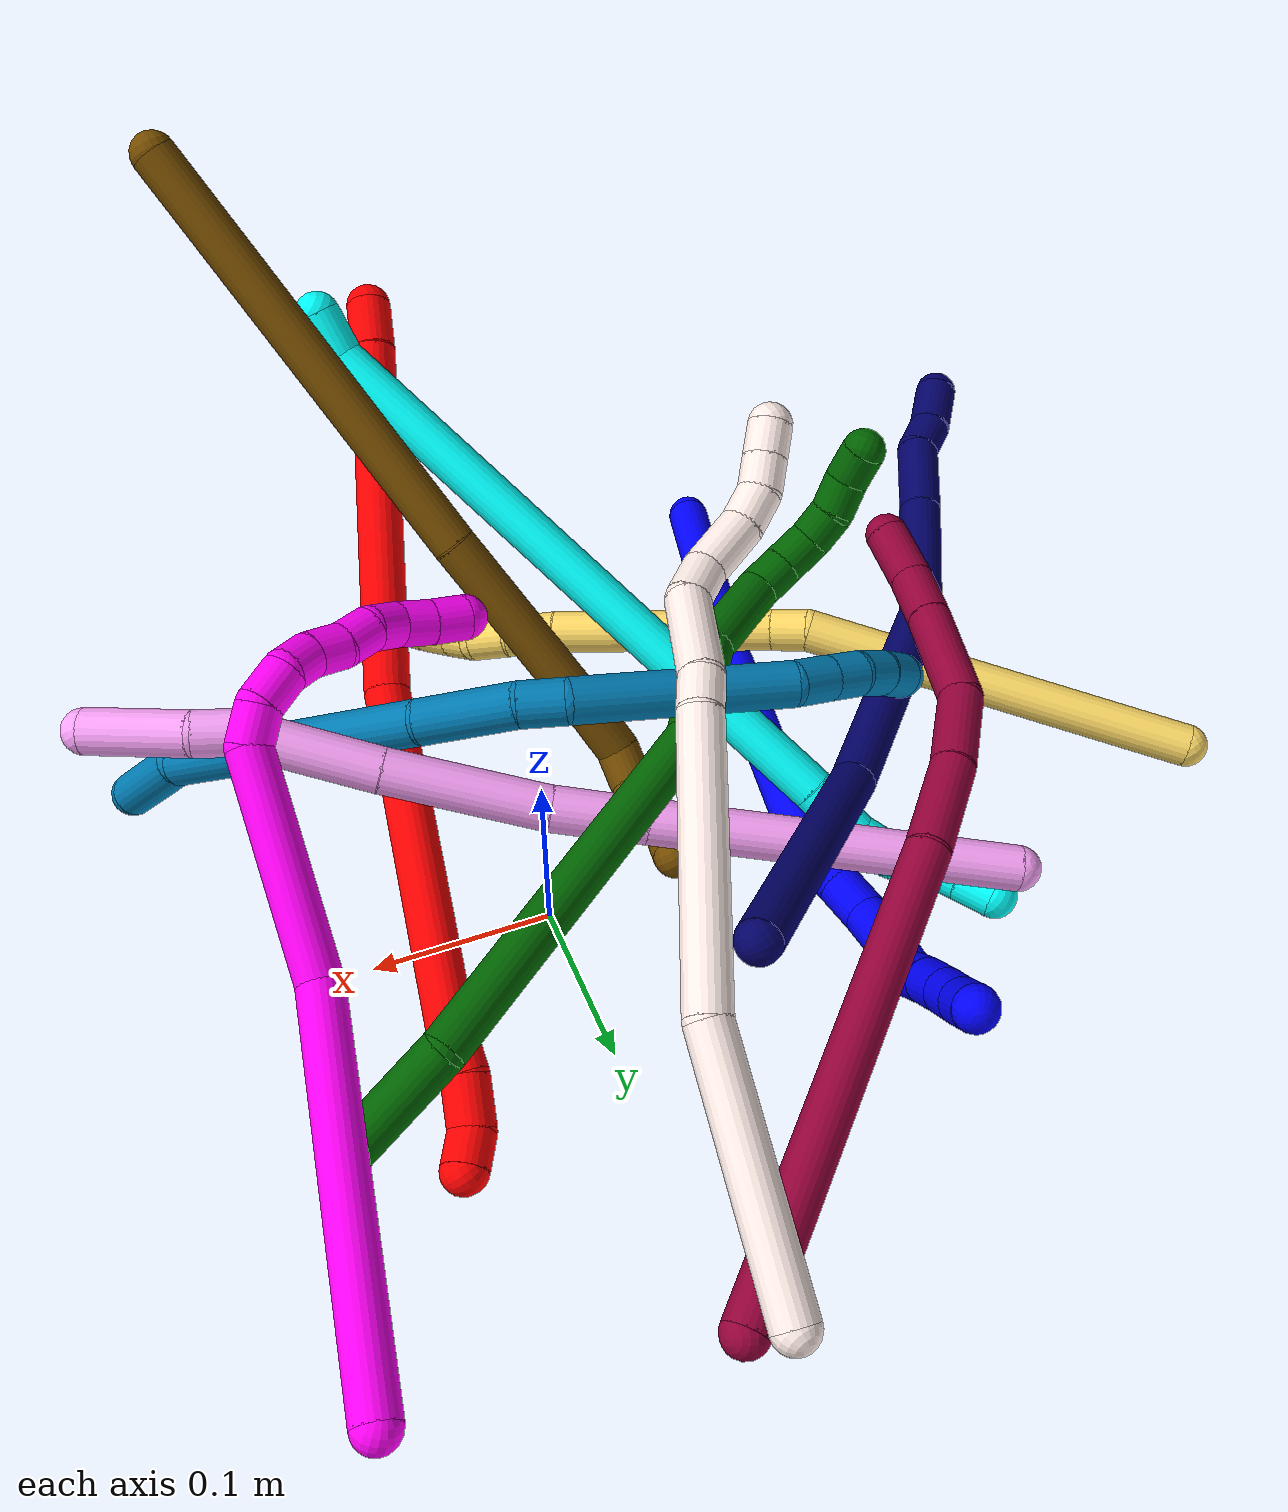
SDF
<sdf version="1.7">
 <world name="default">
  <plugin name="TubeGeneratorPlugin" filename="libtube_generator_plugin.so"/>
  <model name="photoneo_s_sensor">
   <static>1</static>
   <pose>0 0 2 1.57079 1.57079 3.14159</pose>
   <link name="link">
    <inertial><mass>0.1</mass></inertial>
    <sensor name="sensor" type="depth">
     <update_rate>30</update_rate>
     <camera>
      <horizontal_fov>1.22</horizontal_fov>
      <image><width>1920</width><height>1200</height><format>B8G8R8</format></image>
      <clip><near>0.1</near><far>4</far></clip>
      <depth_camera><output>points</output></depth_camera>
     </camera>
     <plugin name="camera_plugin" filename="libgazebo_ros_depth_camera.so">
      <baseline>0.2</baseline>
      <alwaysOn>1</alwaysOn>
      <updateRate>0.0</updateRate>
      <cameraName>camera_ir</cameraName>
      <imageTopicName>/camera/color/image_raw</imageTopicName>
      <cameraInfoTopicName>/camera/color/camera_info</cameraInfoTopicName>
      <depthImageTopicName>/camera/depth/image_raw</depthImageTopicName>
      <depthImageCameraInfoTopicName>/camera/depth/camera_info</depthImageCameraInfoTopicName>
      <pointCloudTopicName>/camera/depth/points</pointCloudTopicName>
      <frameName>fr_optical</frameName>
      <pointCloudCutoff>0.1</pointCloudCutoff>
      <pointCloudCutoffMax>2.0</pointCloudCutoffMax>
      <distortionK1>0</distortionK1>
      <distortionK2>0</distortionK2>
      <distortionK3>0</distortionK3>
      <distortionT1>0</distortionT1>
      <distortionT2>0</distortionT2>
      <CxPrime>0</CxPrime>
      <Cx>0</Cx>
      <Cy>0</Cy>
      <focalLength>0</focalLength>
      <hackBaseline>0</hackBaseline>
     </plugin>
    </sensor>
   </link>
  </model>
  <gravity>0 0 -9.8</gravity>
  <magnetic_field>6e-06 2.3e-05 -4.2e-05</magnetic_field>
  <atmosphere type="adiabatic"/>
  <physics name="default_physics" default="0" type="ode">
   <max_step_size>0.003</max_step_size>
   <real_time_factor>1</real_time_factor>
   <real_time_update_rate>1000</real_time_update_rate>
   <max_contacts>10000</max_contacts>
   <ode>
    <solver>
     <type>quick</type>
     <iters>100</iters>
     <sor>1.3</sor>
     <use_dynamic_moi_rescaling>0</use_dynamic_moi_rescaling>
    </solver>
    <constraints>
     <contact_max_correcting_vel>0</contact_max_correcting_vel>
     <contact_surface_layer>0.001</contact_surface_layer>
     <cfm>0</cfm>
     <erp>0.2</erp>
    </constraints>
   </ode>
  </physics>
  <scene><ambient>0.4 0.4 0.4 1</ambient><background>0.7 0.7 0.7 1</background><shadows>0</shadows></scene>
  <audio><device>default</device></audio>
  <spherical_coordinates>
   <surface_model>EARTH_WGS84</surface_model>
   <latitude_deg>0</latitude_deg>
   <longitude_deg>0</longitude_deg>
   <elevation>0</elevation>
   <heading_deg>0</heading_deg>
  </spherical_coordinates>
  <model name="bin">
   <static>1</static>
   <link name="bottom">
    <collision name="collision-bottom">
     <pose>0 0 -0.01 0 -0 0</pose>
     <geometry><box><size>0.8 0.6 0.02</size></box></geometry>
     <surface>
      <friction><ode><mu>100</mu><mu2>100</mu2></ode></friction>
      <contact><collide_bitmask>65535</collide_bitmask></contact>
     </surface>
    </collision>
   </link>
   <link name="west_wall">
    <collision name="collision-west_wall">
     <pose>-0.41 0 0.1 0 -0 0</pose>
     <geometry><box><size>0.02 0.6 0.2</size></box></geometry>
     <surface>
      <friction><ode><mu>100</mu><mu2>100</mu2></ode></friction>
      <contact><collide_bitmask>65535</collide_bitmask></contact>
     </surface>
    </collision>
   </link>
   <link name="east_wall">
    <collision name="collision-east_wall">
     <pose>0.41 0 0.1 0 -0 0</pose>
     <geometry><box><size>0.02 0.6 0.2</size></box></geometry>
     <surface>
      <friction><ode><mu>100</mu><mu2>100</mu2></ode></friction>
      <contact><collide_bitmask>65535</collide_bitmask></contact>
     </surface>
    </collision>
   </link>
   <link name="south_wall">
    <collision name="collision-south_wall">
     <pose>0 -0.31 0.1 0 -0 0</pose>
     <geometry><box><size>0.8 0.02 0.2</size></box></geometry>
     <surface>
      <friction><ode><mu>100</mu><mu2>100</mu2></ode></friction>
      <contact><collide_bitmask>65535</collide_bitmask></contact>
     </surface>
    </collision>
   </link>
   <link name="north_wall">
    <collision name="collision-north_wall">
     <pose>0 0.31 0.1 0 -0 0</pose>
     <geometry><box><size>0.8 0.02 0.2</size></box></geometry>
     <surface>
      <friction><ode><mu>100</mu><mu2>100</mu2></ode></friction>
      <contact><collide_bitmask>65535</collide_bitmask></contact>
     </surface>
    </collision>
   </link>
  </model>
  <model name="1">
   <static>0</static>
   <link name="1">
    <collision name="collision-cylinder-e_1_1_4">
     <pose>-0.004392 0.025445 -0.071295 -2.79879 -0.057948 0.331778</pose>
     <geometry><cylinder><radius>0.0125</radius><length>0.151654</length></cylinder></geometry>
     <surface>
      <friction><ode><mu>1.16</mu><mu2>1.16</mu2><slip1>0</slip1><slip2>0</slip2></ode></friction>
      <contact><ode><kp>1e+06</kp><kd>1</kd><max_vel>0</max_vel><min_depth>0.001</min_depth></ode></contact>
     </surface>
    </collision>
    <visual name="visual-cylinder-e_1_1_4">
     <pose>-0.004392 0.025445 -0.071295 -2.79879 -0.057948 0.331778</pose>
     <geometry><cylinder><radius>0.0125</radius><length>0.151654</length></cylinder></geometry>
     <material><ambient>0 0 1 1</ambient></material>
    </visual>
    <collision name="collision-cylinder-e_2_4_5">
     <pose>-0.011287 0.085624 -0.215788 -2.69853 -0.030896 0.136972</pose>
     <geometry><cylinder><radius>0.0125</radius><length>0.162118</length></cylinder></geometry>
     <surface>
      <friction><ode><mu>1.16</mu><mu2>1.16</mu2><slip1>0</slip1><slip2>0</slip2></ode></friction>
      <contact><ode><kp>1e+06</kp><kd>1</kd><max_vel>0</max_vel><min_depth>0.001</min_depth></ode></contact>
     </surface>
    </collision>
    <visual name="visual-cylinder-e_2_4_5">
     <pose>-0.011287 0.085624 -0.215788 -2.69853 -0.030896 0.136972</pose>
     <geometry><cylinder><radius>0.0125</radius><length>0.162118</length></cylinder></geometry>
     <material><ambient>0 0 1 1</ambient></material>
    </visual>
    <collision name="collision-cylinder-e_3_5_6">
     <pose>-0.010954 0.130009 -0.297068 -2.26803 0.221698 -0.468091</pose>
     <geometry><cylinder><radius>0.0125</radius><length>0.025808</length></cylinder></geometry>
     <surface>
      <friction><ode><mu>1.16</mu><mu2>1.16</mu2><slip1>0</slip1><slip2>0</slip2></ode></friction>
      <contact><ode><kp>1e+06</kp><kd>1</kd><max_vel>0</max_vel><min_depth>0.001</min_depth></ode></contact>
     </surface>
    </collision>
    <visual name="visual-cylinder-e_3_5_6">
     <pose>-0.010954 0.130009 -0.297068 -2.26803 0.221698 -0.468091</pose>
     <geometry><cylinder><radius>0.0125</radius><length>0.025808</length></cylinder></geometry>
     <material><ambient>0 0 1 1</ambient></material>
    </visual>
    <collision name="collision-cylinder-e_4_6_7">
     <pose>-0.005341 0.147247 -0.31463 -2.46657 0.224739 -0.622213</pose>
     <geometry><cylinder><radius>0.0125</radius><length>0.02491</length></cylinder></geometry>
     <surface>
      <friction><ode><mu>1.16</mu><mu2>1.16</mu2><slip1>0</slip1><slip2>0</slip2></ode></friction>
      <contact><ode><kp>1e+06</kp><kd>1</kd><max_vel>0</max_vel><min_depth>0.001</min_depth></ode></contact>
     </surface>
    </collision>
    <visual name="visual-cylinder-e_4_6_7">
     <pose>-0.005341 0.147247 -0.31463 -2.46657 0.224739 -0.622213</pose>
     <geometry><cylinder><radius>0.0125</radius><length>0.02491</length></cylinder></geometry>
     <material><ambient>0 0 1 1</ambient></material>
    </visual>
    <collision name="collision-cylinder-e_5_7_8">
     <pose>9.2e-05 0.159648 -0.335402 -2.7387 0.213161 -0.965146</pose>
     <geometry><cylinder><radius>0.0125</radius><length>0.02512</length></cylinder></geometry>
     <surface>
      <friction><ode><mu>1.16</mu><mu2>1.16</mu2><slip1>0</slip1><slip2>0</slip2></ode></friction>
      <contact><ode><kp>1e+06</kp><kd>1</kd><max_vel>0</max_vel><min_depth>0.001</min_depth></ode></contact>
     </surface>
    </collision>
    <visual name="visual-cylinder-e_5_7_8">
     <pose>9.2e-05 0.159648 -0.335402 -2.7387 0.213161 -0.965146</pose>
     <geometry><cylinder><radius>0.0125</radius><length>0.02512</length></cylinder></geometry>
     <material><ambient>0 0 1 1</ambient></material>
    </visual>
    <collision name="collision-cylinder-e_6_8_9">
     <pose>0.004913 0.169073 -0.359097 -2.78557 0.162071 -0.848026</pose>
     <geometry><cylinder><radius>0.0125</radius><length>0.026816</length></cylinder></geometry>
     <surface>
      <friction><ode><mu>1.16</mu><mu2>1.16</mu2><slip1>0</slip1><slip2>0</slip2></ode></friction>
      <contact><ode><kp>1e+06</kp><kd>1</kd><max_vel>0</max_vel><min_depth>0.001</min_depth></ode></contact>
     </surface>
    </collision>
    <visual name="visual-cylinder-e_6_8_9">
     <pose>0.004913 0.169073 -0.359097 -2.78557 0.162071 -0.848026</pose>
     <geometry><cylinder><radius>0.0125</radius><length>0.026816</length></cylinder></geometry>
     <material><ambient>0 0 1 1</ambient></material>
    </visual>
    <collision name="collision-cylinder-e_7_9_10">
     <pose>0.011442 0.172761 -0.38059 3.04029 0.445739 2.70146</pose>
     <geometry><cylinder><radius>0.0125</radius><length>0.020253</length></cylinder></geometry>
     <surface>
      <friction><ode><mu>1.16</mu><mu2>1.16</mu2><slip1>0</slip1><slip2>0</slip2></ode></friction>
      <contact><ode><kp>1e+06</kp><kd>1</kd><max_vel>0</max_vel><min_depth>0.001</min_depth></ode></contact>
     </surface>
    </collision>
    <visual name="visual-cylinder-e_7_9_10">
     <pose>0.011442 0.172761 -0.38059 3.04029 0.445739 2.70146</pose>
     <geometry><cylinder><radius>0.0125</radius><length>0.020253</length></cylinder></geometry>
     <material><ambient>0 0 1 1</ambient></material>
    </visual>
    <collision name="collision-cylinder-e_8_10_11">
     <pose>0.020238 0.171413 -0.399817 3.09984 0.411719 2.94227</pose>
     <geometry><cylinder><radius>0.0125</radius><length>0.022143</length></cylinder></geometry>
     <surface>
      <friction><ode><mu>1.16</mu><mu2>1.16</mu2><slip1>0</slip1><slip2>0</slip2></ode></friction>
      <contact><ode><kp>1e+06</kp><kd>1</kd><max_vel>0</max_vel><min_depth>0.001</min_depth></ode></contact>
     </surface>
    </collision>
    <visual name="visual-cylinder-e_8_10_11">
     <pose>0.020238 0.171413 -0.399817 3.09984 0.411719 2.94227</pose>
     <geometry><cylinder><radius>0.0125</radius><length>0.022143</length></cylinder></geometry>
     <material><ambient>0 0 1 1</ambient></material>
    </visual>
    <collision name="collision-cylinder-e_9_11_12">
     <pose>0.028309 0.17019 -0.419352 3.05667 0.368345 2.6931</pose>
     <geometry><cylinder><radius>0.0125</radius><length>0.020217</length></cylinder></geometry>
     <surface>
      <friction><ode><mu>1.16</mu><mu2>1.16</mu2><slip1>0</slip1><slip2>0</slip2></ode></friction>
      <contact><ode><kp>1e+06</kp><kd>1</kd><max_vel>0</max_vel><min_depth>0.001</min_depth></ode></contact>
     </surface>
    </collision>
    <visual name="visual-cylinder-e_9_11_12">
     <pose>0.028309 0.17019 -0.419352 3.05667 0.368345 2.6931</pose>
     <geometry><cylinder><radius>0.0125</radius><length>0.020217</length></cylinder></geometry>
     <material><ambient>0 0 1 1</ambient></material>
    </visual>
    <collision name="collision-cylinder-e_10_12_2">
     <pose>0.03566 0.167319 -0.438328 2.92866 0.361967 2.08441</pose>
     <geometry><cylinder><radius>0.0125</radius><length>0.02096</length></cylinder></geometry>
     <surface>
      <friction><ode><mu>1.16</mu><mu2>1.16</mu2><slip1>0</slip1><slip2>0</slip2></ode></friction>
      <contact><ode><kp>1e+06</kp><kd>1</kd><max_vel>0</max_vel><min_depth>0.001</min_depth></ode></contact>
     </surface>
    </collision>
    <visual name="visual-cylinder-e_10_12_2">
     <pose>0.03566 0.167319 -0.438328 2.92866 0.361967 2.08441</pose>
     <geometry><cylinder><radius>0.0125</radius><length>0.02096</length></cylinder></geometry>
     <material><ambient>0 0 1 1</ambient></material>
    </visual>
    <collision name="collision-sphere-2">
     <pose>0.039371 0.165247 -0.447908 0 -0 0</pose>
     <geometry><sphere><radius>0.0125</radius></sphere></geometry>
     <surface>
      <friction><ode><mu>1.16</mu><mu2>1.16</mu2><slip1>0</slip1><slip2>0</slip2></ode></friction>
      <contact><ode><kp>1e+06</kp><kd>1</kd><max_vel>0</max_vel><min_depth>0.001</min_depth></ode></contact>
     </surface>
    </collision>
    <visual name="visual-sphere-2">
     <pose>0.039371 0.165247 -0.447908 0 -0 0</pose>
     <geometry><sphere><radius>0.0125</radius></sphere></geometry>
     <material><ambient>0 0 1 1</ambient></material>
    </visual>
    <collision name="collision-sphere-12">
     <pose>0.031949 0.16939 -0.428748 0 -0 0</pose>
     <geometry><sphere><radius>0.0125</radius></sphere></geometry>
     <surface>
      <friction><ode><mu>1.16</mu><mu2>1.16</mu2><slip1>0</slip1><slip2>0</slip2></ode></friction>
      <contact><ode><kp>1e+06</kp><kd>1</kd><max_vel>0</max_vel><min_depth>0.001</min_depth></ode></contact>
     </surface>
    </collision>
    <visual name="visual-sphere-12">
     <pose>0.031949 0.16939 -0.428748 0 -0 0</pose>
     <geometry><sphere><radius>0.0125</radius></sphere></geometry>
     <material><ambient>0 0 1 1</ambient></material>
    </visual>
    <collision name="collision-sphere-11">
     <pose>0.024669 0.17099 -0.409955 0 -0 0</pose>
     <geometry><sphere><radius>0.0125</radius></sphere></geometry>
     <surface>
      <friction><ode><mu>1.16</mu><mu2>1.16</mu2><slip1>0</slip1><slip2>0</slip2></ode></friction>
      <contact><ode><kp>1e+06</kp><kd>1</kd><max_vel>0</max_vel><min_depth>0.001</min_depth></ode></contact>
     </surface>
    </collision>
    <visual name="visual-sphere-11">
     <pose>0.024669 0.17099 -0.409955 0 -0 0</pose>
     <geometry><sphere><radius>0.0125</radius></sphere></geometry>
     <material><ambient>0 0 1 1</ambient></material>
    </visual>
    <collision name="collision-sphere-10">
     <pose>0.015808 0.171837 -0.38968 0 -0 0</pose>
     <geometry><sphere><radius>0.0125</radius></sphere></geometry>
     <surface>
      <friction><ode><mu>1.16</mu><mu2>1.16</mu2><slip1>0</slip1><slip2>0</slip2></ode></friction>
      <contact><ode><kp>1e+06</kp><kd>1</kd><max_vel>0</max_vel><min_depth>0.001</min_depth></ode></contact>
     </surface>
    </collision>
    <visual name="visual-sphere-10">
     <pose>0.015808 0.171837 -0.38968 0 -0 0</pose>
     <geometry><sphere><radius>0.0125</radius></sphere></geometry>
     <material><ambient>0 0 1 1</ambient></material>
    </visual>
    <collision name="collision-sphere-9">
     <pose>0.007076 0.173685 -0.3715 0 -0 0</pose>
     <geometry><sphere><radius>0.0125</radius></sphere></geometry>
     <surface>
      <friction><ode><mu>1.16</mu><mu2>1.16</mu2><slip1>0</slip1><slip2>0</slip2></ode></friction>
      <contact><ode><kp>1e+06</kp><kd>1</kd><max_vel>0</max_vel><min_depth>0.001</min_depth></ode></contact>
     </surface>
    </collision>
    <visual name="visual-sphere-9">
     <pose>0.007076 0.173685 -0.3715 0 -0 0</pose>
     <geometry><sphere><radius>0.0125</radius></sphere></geometry>
     <material><ambient>0 0 1 1</ambient></material>
    </visual>
    <collision name="collision-sphere-4">
     <pose>-0.008783 0.05089 -0.14259 0 -0 0</pose>
     <geometry><sphere><radius>0.0125</radius></sphere></geometry>
     <surface>
      <friction><ode><mu>1.16</mu><mu2>1.16</mu2><slip1>0</slip1><slip2>0</slip2></ode></friction>
      <contact><ode><kp>1e+06</kp><kd>1</kd><max_vel>0</max_vel><min_depth>0.001</min_depth></ode></contact>
     </surface>
    </collision>
    <visual name="visual-sphere-4">
     <pose>-0.008783 0.05089 -0.14259 0 -0 0</pose>
     <geometry><sphere><radius>0.0125</radius></sphere></geometry>
     <material><ambient>0 0 1 1</ambient></material>
    </visual>
    <collision name="collision-sphere-1">
     <geometry><sphere><radius>0.0125</radius></sphere></geometry>
     <surface>
      <friction><ode><mu>1.16</mu><mu2>1.16</mu2><slip1>0</slip1><slip2>0</slip2></ode></friction>
      <contact><ode><kp>1e+06</kp><kd>1</kd><max_vel>0</max_vel><min_depth>0.001</min_depth></ode></contact>
     </surface>
    </collision>
    <visual name="visual-sphere-1">
     <geometry><sphere><radius>0.0125</radius></sphere></geometry>
     <material><ambient>0 0 1 1</ambient></material>
    </visual>
    <collision name="collision-sphere-8">
     <pose>0.002749 0.164461 -0.346695 0 -0 0</pose>
     <geometry><sphere><radius>0.0125</radius></sphere></geometry>
     <surface>
      <friction><ode><mu>1.16</mu><mu2>1.16</mu2><slip1>0</slip1><slip2>0</slip2></ode></friction>
      <contact><ode><kp>1e+06</kp><kd>1</kd><max_vel>0</max_vel><min_depth>0.001</min_depth></ode></contact>
     </surface>
    </collision>
    <visual name="visual-sphere-8">
     <pose>0.002749 0.164461 -0.346695 0 -0 0</pose>
     <geometry><sphere><radius>0.0125</radius></sphere></geometry>
     <material><ambient>0 0 1 1</ambient></material>
    </visual>
    <collision name="collision-sphere-5">
     <pose>-0.013791 0.120358 -0.288985 0 -0 0</pose>
     <geometry><sphere><radius>0.0125</radius></sphere></geometry>
     <surface>
      <friction><ode><mu>1.16</mu><mu2>1.16</mu2><slip1>0</slip1><slip2>0</slip2></ode></friction>
      <contact><ode><kp>1e+06</kp><kd>1</kd><max_vel>0</max_vel><min_depth>0.001</min_depth></ode></contact>
     </surface>
    </collision>
    <visual name="visual-sphere-5">
     <pose>-0.013791 0.120358 -0.288985 0 -0 0</pose>
     <geometry><sphere><radius>0.0125</radius></sphere></geometry>
     <material><ambient>0 0 1 1</ambient></material>
    </visual>
    <collision name="collision-sphere-6">
     <pose>-0.008116 0.139659 -0.305151 0 -0 0</pose>
     <geometry><sphere><radius>0.0125</radius></sphere></geometry>
     <surface>
      <friction><ode><mu>1.16</mu><mu2>1.16</mu2><slip1>0</slip1><slip2>0</slip2></ode></friction>
      <contact><ode><kp>1e+06</kp><kd>1</kd><max_vel>0</max_vel><min_depth>0.001</min_depth></ode></contact>
     </surface>
    </collision>
    <visual name="visual-sphere-6">
     <pose>-0.008116 0.139659 -0.305151 0 -0 0</pose>
     <geometry><sphere><radius>0.0125</radius></sphere></geometry>
     <material><ambient>0 0 1 1</ambient></material>
    </visual>
    <collision name="collision-sphere-7">
     <pose>-0.002565 0.154834 -0.324109 0 -0 0</pose>
     <geometry><sphere><radius>0.0125</radius></sphere></geometry>
     <surface>
      <friction><ode><mu>1.16</mu><mu2>1.16</mu2><slip1>0</slip1><slip2>0</slip2></ode></friction>
      <contact><ode><kp>1e+06</kp><kd>1</kd><max_vel>0</max_vel><min_depth>0.001</min_depth></ode></contact>
     </surface>
    </collision>
    <visual name="visual-sphere-7">
     <pose>-0.002565 0.154834 -0.324109 0 -0 0</pose>
     <geometry><sphere><radius>0.0125</radius></sphere></geometry>
     <material><ambient>0 0 1 1</ambient></material>
    </visual>
    <inertial>
     <pose>-0.001556 0.0951 -0.227162 0 -0 0</pose>
     <mass>0.5</mass>
     <inertia>
      <ixx>0.000785</ixx>
      <ixy>0</ixy>
      <ixz>0</ixz>
      <iyy>-0.000429</iyy>
      <iyz>0</iyz>
      <izz>-0.00027</izz>
     </inertia>
    </inertial>
   </link>
   <pose>-0.199631 -0.283556 0.011497 -2.02134 -0.601897 3.02966</pose>
  </model>
  <model name="2">
   <static>0</static>
   <link name="2">
    <collision name="collision-cylinder-e_1_1_4">
     <pose>0.000365 0.013297 -0.006179 -2.00579 0.024873 -0.038983</pose>
     <geometry><cylinder><radius>0.0125</radius><length>0.029335</length></cylinder></geometry>
     <surface>
      <friction><ode><mu>1.16</mu><mu2>1.16</mu2><slip1>0</slip1><slip2>0</slip2></ode></friction>
      <contact><ode><kp>1e+06</kp><kd>1</kd><max_vel>0</max_vel><min_depth>0.001</min_depth></ode></contact>
     </surface>
    </collision>
    <visual name="visual-cylinder-e_1_1_4">
     <pose>0.000365 0.013297 -0.006179 -2.00579 0.024873 -0.038983</pose>
     <geometry><cylinder><radius>0.0125</radius><length>0.029335</length></cylinder></geometry>
     <material><ambient>1 0 0 1</ambient></material>
    </visual>
    <collision name="collision-cylinder-e_2_4_5">
     <pose>-0.00108 0.116728 -0.0621 -2.07507 -0.017579 0.029779</pose>
     <geometry><cylinder><radius>0.0125</radius><length>0.205928</length></cylinder></geometry>
     <surface>
      <friction><ode><mu>1.16</mu><mu2>1.16</mu2><slip1>0</slip1><slip2>0</slip2></ode></friction>
      <contact><ode><kp>1e+06</kp><kd>1</kd><max_vel>0</max_vel><min_depth>0.001</min_depth></ode></contact>
     </surface>
    </collision>
    <visual name="visual-cylinder-e_2_4_5">
     <pose>-0.00108 0.116728 -0.0621 -2.07507 -0.017579 0.029779</pose>
     <geometry><cylinder><radius>0.0125</radius><length>0.205928</length></cylinder></geometry>
     <material><ambient>1 0 0 1</ambient></material>
    </visual>
    <collision name="collision-cylinder-e_3_5_6">
     <pose>0.009135 0.299089 -0.143398 -1.90047 0.122748 -0.171528</pose>
     <geometry><cylinder><radius>0.0125</radius><length>0.196432</length></cylinder></geometry>
     <surface>
      <friction><ode><mu>1.16</mu><mu2>1.16</mu2><slip1>0</slip1><slip2>0</slip2></ode></friction>
      <contact><ode><kp>1e+06</kp><kd>1</kd><max_vel>0</max_vel><min_depth>0.001</min_depth></ode></contact>
     </surface>
    </collision>
    <visual name="visual-cylinder-e_3_5_6">
     <pose>0.009135 0.299089 -0.143398 -1.90047 0.122748 -0.171528</pose>
     <geometry><cylinder><radius>0.0125</radius><length>0.196432</length></cylinder></geometry>
     <material><ambient>1 0 0 1</ambient></material>
    </visual>
    <collision name="collision-cylinder-e_4_6_7">
     <pose>0.02107 0.401604 -0.177452 -1.80888 -0.008561 0.010887</pose>
     <geometry><cylinder><radius>0.0125</radius><length>0.021175</length></cylinder></geometry>
     <surface>
      <friction><ode><mu>1.16</mu><mu2>1.16</mu2><slip1>0</slip1><slip2>0</slip2></ode></friction>
      <contact><ode><kp>1e+06</kp><kd>1</kd><max_vel>0</max_vel><min_depth>0.001</min_depth></ode></contact>
     </surface>
    </collision>
    <visual name="visual-cylinder-e_4_6_7">
     <pose>0.02107 0.401604 -0.177452 -1.80888 -0.008561 0.010887</pose>
     <geometry><cylinder><radius>0.0125</radius><length>0.021175</length></cylinder></geometry>
     <material><ambient>1 0 0 1</ambient></material>
    </visual>
    <collision name="collision-cylinder-e_5_7_8">
     <pose>0.02074 0.424263 -0.18551 -1.99333 -0.017643 0.027275</pose>
     <geometry><cylinder><radius>0.0125</radius><length>0.02713</length></cylinder></geometry>
     <surface>
      <friction><ode><mu>1.16</mu><mu2>1.16</mu2><slip1>0</slip1><slip2>0</slip2></ode></friction>
      <contact><ode><kp>1e+06</kp><kd>1</kd><max_vel>0</max_vel><min_depth>0.001</min_depth></ode></contact>
     </surface>
    </collision>
    <visual name="visual-cylinder-e_5_7_8">
     <pose>0.02074 0.424263 -0.18551 -1.99333 -0.017643 0.027275</pose>
     <geometry><cylinder><radius>0.0125</radius><length>0.02713</length></cylinder></geometry>
     <material><ambient>1 0 0 1</ambient></material>
    </visual>
    <collision name="collision-cylinder-e_6_8_2">
     <pose>0.023317 0.444133 -0.197057 -2.24432 0.285489 -0.580286</pose>
     <geometry><cylinder><radius>0.0125</radius><length>0.020001</length></cylinder></geometry>
     <surface>
      <friction><ode><mu>1.16</mu><mu2>1.16</mu2><slip1>0</slip1><slip2>0</slip2></ode></friction>
      <contact><ode><kp>1e+06</kp><kd>1</kd><max_vel>0</max_vel><min_depth>0.001</min_depth></ode></contact>
     </surface>
    </collision>
    <visual name="visual-cylinder-e_6_8_2">
     <pose>0.023317 0.444133 -0.197057 -2.24432 0.285489 -0.580286</pose>
     <geometry><cylinder><radius>0.0125</radius><length>0.020001</length></cylinder></geometry>
     <material><ambient>1 0 0 1</ambient></material>
    </visual>
    <collision name="collision-sphere-2">
     <pose>0.026134 0.451634 -0.203043 0 -0 0</pose>
     <geometry><sphere><radius>0.0125</radius></sphere></geometry>
     <surface>
      <friction><ode><mu>1.16</mu><mu2>1.16</mu2><slip1>0</slip1><slip2>0</slip2></ode></friction>
      <contact><ode><kp>1e+06</kp><kd>1</kd><max_vel>0</max_vel><min_depth>0.001</min_depth></ode></contact>
     </surface>
    </collision>
    <visual name="visual-sphere-2">
     <pose>0.026134 0.451634 -0.203043 0 -0 0</pose>
     <geometry><sphere><radius>0.0125</radius></sphere></geometry>
     <material><ambient>1 0 0 1</ambient></material>
    </visual>
    <collision name="collision-sphere-4">
     <pose>0.00073 0.026594 -0.012358 0 -0 0</pose>
     <geometry><sphere><radius>0.0125</radius></sphere></geometry>
     <surface>
      <friction><ode><mu>1.16</mu><mu2>1.16</mu2><slip1>0</slip1><slip2>0</slip2></ode></friction>
      <contact><ode><kp>1e+06</kp><kd>1</kd><max_vel>0</max_vel><min_depth>0.001</min_depth></ode></contact>
     </surface>
    </collision>
    <visual name="visual-sphere-4">
     <pose>0.00073 0.026594 -0.012358 0 -0 0</pose>
     <geometry><sphere><radius>0.0125</radius></sphere></geometry>
     <material><ambient>1 0 0 1</ambient></material>
    </visual>
    <collision name="collision-sphere-1">
     <geometry><sphere><radius>0.0125</radius></sphere></geometry>
     <surface>
      <friction><ode><mu>1.16</mu><mu2>1.16</mu2><slip1>0</slip1><slip2>0</slip2></ode></friction>
      <contact><ode><kp>1e+06</kp><kd>1</kd><max_vel>0</max_vel><min_depth>0.001</min_depth></ode></contact>
     </surface>
    </collision>
    <visual name="visual-sphere-1">
     <geometry><sphere><radius>0.0125</radius></sphere></geometry>
     <material><ambient>1 0 0 1</ambient></material>
    </visual>
    <collision name="collision-sphere-8">
     <pose>0.020501 0.436633 -0.191072 0 -0 0</pose>
     <geometry><sphere><radius>0.0125</radius></sphere></geometry>
     <surface>
      <friction><ode><mu>1.16</mu><mu2>1.16</mu2><slip1>0</slip1><slip2>0</slip2></ode></friction>
      <contact><ode><kp>1e+06</kp><kd>1</kd><max_vel>0</max_vel><min_depth>0.001</min_depth></ode></contact>
     </surface>
    </collision>
    <visual name="visual-sphere-8">
     <pose>0.020501 0.436633 -0.191072 0 -0 0</pose>
     <geometry><sphere><radius>0.0125</radius></sphere></geometry>
     <material><ambient>1 0 0 1</ambient></material>
    </visual>
    <collision name="collision-sphere-5">
     <pose>-0.00289 0.206861 -0.111842 0 -0 0</pose>
     <geometry><sphere><radius>0.0125</radius></sphere></geometry>
     <surface>
      <friction><ode><mu>1.16</mu><mu2>1.16</mu2><slip1>0</slip1><slip2>0</slip2></ode></friction>
      <contact><ode><kp>1e+06</kp><kd>1</kd><max_vel>0</max_vel><min_depth>0.001</min_depth></ode></contact>
     </surface>
    </collision>
    <visual name="visual-sphere-5">
     <pose>-0.00289 0.206861 -0.111842 0 -0 0</pose>
     <geometry><sphere><radius>0.0125</radius></sphere></geometry>
     <material><ambient>1 0 0 1</ambient></material>
    </visual>
    <collision name="collision-sphere-6">
     <pose>0.021161 0.391316 -0.174955 0 -0 0</pose>
     <geometry><sphere><radius>0.0125</radius></sphere></geometry>
     <surface>
      <friction><ode><mu>1.16</mu><mu2>1.16</mu2><slip1>0</slip1><slip2>0</slip2></ode></friction>
      <contact><ode><kp>1e+06</kp><kd>1</kd><max_vel>0</max_vel><min_depth>0.001</min_depth></ode></contact>
     </surface>
    </collision>
    <visual name="visual-sphere-6">
     <pose>0.021161 0.391316 -0.174955 0 -0 0</pose>
     <geometry><sphere><radius>0.0125</radius></sphere></geometry>
     <material><ambient>1 0 0 1</ambient></material>
    </visual>
    <collision name="collision-sphere-7">
     <pose>0.020979 0.411893 -0.179948 0 -0 0</pose>
     <geometry><sphere><radius>0.0125</radius></sphere></geometry>
     <surface>
      <friction><ode><mu>1.16</mu><mu2>1.16</mu2><slip1>0</slip1><slip2>0</slip2></ode></friction>
      <contact><ode><kp>1e+06</kp><kd>1</kd><max_vel>0</max_vel><min_depth>0.001</min_depth></ode></contact>
     </surface>
    </collision>
    <visual name="visual-sphere-7">
     <pose>0.020979 0.411893 -0.179948 0 -0 0</pose>
     <geometry><sphere><radius>0.0125</radius></sphere></geometry>
     <material><ambient>1 0 0 1</ambient></material>
    </visual>
    <inertial>
     <pose>0.006116 0.224151 -0.107738 0 -0 0</pose>
     <mass>0.5</mass>
     <inertia>
      <ixx>0.001284</ixx>
      <ixy>0</ixy>
      <ixz>0</ixz>
      <iyy>-0.000602</iyy>
      <iyz>0</iyz>
      <izz>-0.001334</izz>
     </inertia>
    </inertial>
   </link>
   <pose>-0.004604 -0.298173 0.211907 -0.703494 -1.0483 0.86229</pose>
  </model>
  <model name="3">
   <static>0</static>
   <link name="3">
    <collision name="collision-cylinder-e_1_1_4">
     <pose>0.000468 0.008038 -0.011132 -2.5162 0.034078 -0.105318</pose>
     <geometry><cylinder><radius>0.0125</radius><length>0.027477</length></cylinder></geometry>
     <surface>
      <friction><ode><mu>1.16</mu><mu2>1.16</mu2><slip1>0</slip1><slip2>0</slip2></ode></friction>
      <contact><ode><kp>1e+06</kp><kd>1</kd><max_vel>0</max_vel><min_depth>0.001</min_depth></ode></contact>
     </surface>
    </collision>
    <visual name="visual-cylinder-e_1_1_4">
     <pose>0.000468 0.008038 -0.011132 -2.5162 0.034078 -0.105318</pose>
     <geometry><cylinder><radius>0.0125</radius><length>0.027477</length></cylinder></geometry>
     <material><ambient>0.003922 1 0.996078 1</ambient></material>
    </visual>
    <collision name="collision-cylinder-e_2_4_5">
     <pose>-0.056517 0.093385 -0.170554 -2.66102 -0.330923 1.19645</pose>
     <geometry><cylinder><radius>0.0125</radius><length>0.353652</length></cylinder></geometry>
     <surface>
      <friction><ode><mu>1.16</mu><mu2>1.16</mu2><slip1>0</slip1><slip2>0</slip2></ode></friction>
      <contact><ode><kp>1e+06</kp><kd>1</kd><max_vel>0</max_vel><min_depth>0.001</min_depth></ode></contact>
     </surface>
    </collision>
    <visual name="visual-cylinder-e_2_4_5">
     <pose>-0.056517 0.093385 -0.170554 -2.66102 -0.330923 1.19645</pose>
     <geometry><cylinder><radius>0.0125</radius><length>0.353652</length></cylinder></geometry>
     <material><ambient>0.003922 1 0.996078 1</ambient></material>
    </visual>
    <collision name="collision-cylinder-e_3_5_6">
     <pose>-0.118314 0.178731 -0.333772 -2.64768 -0.250775 0.927282</pose>
     <geometry><cylinder><radius>0.0125</radius><length>0.035004</length></cylinder></geometry>
     <surface>
      <friction><ode><mu>1.16</mu><mu2>1.16</mu2><slip1>0</slip1><slip2>0</slip2></ode></friction>
      <contact><ode><kp>1e+06</kp><kd>1</kd><max_vel>0</max_vel><min_depth>0.001</min_depth></ode></contact>
     </surface>
    </collision>
    <visual name="visual-cylinder-e_3_5_6">
     <pose>-0.118314 0.178731 -0.333772 -2.64768 -0.250775 0.927282</pose>
     <geometry><cylinder><radius>0.0125</radius><length>0.035004</length></cylinder></geometry>
     <material><ambient>0.003922 1 0.996078 1</ambient></material>
    </visual>
    <collision name="collision-cylinder-e_4_6_7">
     <pose>-0.1274 0.190007 -0.358628 -2.82625 -0.426344 1.87458</pose>
     <geometry><cylinder><radius>0.0125</radius><length>0.022937</length></cylinder></geometry>
     <surface>
      <friction><ode><mu>1.16</mu><mu2>1.16</mu2><slip1>0</slip1><slip2>0</slip2></ode></friction>
      <contact><ode><kp>1e+06</kp><kd>1</kd><max_vel>0</max_vel><min_depth>0.001</min_depth></ode></contact>
     </surface>
    </collision>
    <visual name="visual-cylinder-e_4_6_7">
     <pose>-0.1274 0.190007 -0.358628 -2.82625 -0.426344 1.87458</pose>
     <geometry><cylinder><radius>0.0125</radius><length>0.022937</length></cylinder></geometry>
     <material><ambient>0.003922 1 0.996078 1</ambient></material>
    </visual>
    <collision name="collision-cylinder-e_5_7_8">
     <pose>-0.139692 0.193399 -0.375291 -3.11881 -0.842097 3.09073</pose>
     <geometry><cylinder><radius>0.0125</radius><length>0.020238</length></cylinder></geometry>
     <surface>
      <friction><ode><mu>1.16</mu><mu2>1.16</mu2><slip1>0</slip1><slip2>0</slip2></ode></friction>
      <contact><ode><kp>1e+06</kp><kd>1</kd><max_vel>0</max_vel><min_depth>0.001</min_depth></ode></contact>
     </surface>
    </collision>
    <visual name="visual-cylinder-e_5_7_8">
     <pose>-0.139692 0.193399 -0.375291 -3.11881 -0.842097 3.09073</pose>
     <geometry><cylinder><radius>0.0125</radius><length>0.020238</length></cylinder></geometry>
     <material><ambient>0.003922 1 0.996078 1</ambient></material>
    </visual>
    <collision name="collision-cylinder-e_6_8_9">
     <pose>-0.154228 0.196891 -0.388378 -2.65765 -0.772108 2.05016</pose>
     <geometry><cylinder><radius>0.0125</radius><length>0.020028</length></cylinder></geometry>
     <surface>
      <friction><ode><mu>1.16</mu><mu2>1.16</mu2><slip1>0</slip1><slip2>0</slip2></ode></friction>
      <contact><ode><kp>1e+06</kp><kd>1</kd><max_vel>0</max_vel><min_depth>0.001</min_depth></ode></contact>
     </surface>
    </collision>
    <visual name="visual-cylinder-e_6_8_9">
     <pose>-0.154228 0.196891 -0.388378 -2.65765 -0.772108 2.05016</pose>
     <geometry><cylinder><radius>0.0125</radius><length>0.020028</length></cylinder></geometry>
     <material><ambient>0.003922 1 0.996078 1</ambient></material>
    </visual>
    <collision name="collision-cylinder-e_7_9_2">
     <pose>-0.168106 0.203561 -0.401667 -2.69386 -0.730309 2.06729</pose>
     <geometry><cylinder><radius>0.0125</radius><length>0.020664</length></cylinder></geometry>
     <surface>
      <friction><ode><mu>1.16</mu><mu2>1.16</mu2><slip1>0</slip1><slip2>0</slip2></ode></friction>
      <contact><ode><kp>1e+06</kp><kd>1</kd><max_vel>0</max_vel><min_depth>0.001</min_depth></ode></contact>
     </surface>
    </collision>
    <visual name="visual-cylinder-e_7_9_2">
     <pose>-0.168106 0.203561 -0.401667 -2.69386 -0.730309 2.06729</pose>
     <geometry><cylinder><radius>0.0125</radius><length>0.020664</length></cylinder></geometry>
     <material><ambient>0.003922 1 0.996078 1</ambient></material>
    </visual>
    <collision name="collision-sphere-2">
     <pose>-0.174998 0.206893 -0.408605 0 -0 0</pose>
     <geometry><sphere><radius>0.0125</radius></sphere></geometry>
     <surface>
      <friction><ode><mu>1.16</mu><mu2>1.16</mu2><slip1>0</slip1><slip2>0</slip2></ode></friction>
      <contact><ode><kp>1e+06</kp><kd>1</kd><max_vel>0</max_vel><min_depth>0.001</min_depth></ode></contact>
     </surface>
    </collision>
    <visual name="visual-sphere-2">
     <pose>-0.174998 0.206893 -0.408605 0 -0 0</pose>
     <geometry><sphere><radius>0.0125</radius></sphere></geometry>
     <material><ambient>0.003922 1 0.996078 1</ambient></material>
    </visual>
    <collision name="collision-sphere-9">
     <pose>-0.161214 0.200229 -0.394729 0 -0 0</pose>
     <geometry><sphere><radius>0.0125</radius></sphere></geometry>
     <surface>
      <friction><ode><mu>1.16</mu><mu2>1.16</mu2><slip1>0</slip1><slip2>0</slip2></ode></friction>
      <contact><ode><kp>1e+06</kp><kd>1</kd><max_vel>0</max_vel><min_depth>0.001</min_depth></ode></contact>
     </surface>
    </collision>
    <visual name="visual-sphere-9">
     <pose>-0.161214 0.200229 -0.394729 0 -0 0</pose>
     <geometry><sphere><radius>0.0125</radius></sphere></geometry>
     <material><ambient>0.003922 1 0.996078 1</ambient></material>
    </visual>
    <collision name="collision-sphere-4">
     <pose>0.000936 0.016076 -0.022264 0 -0 0</pose>
     <geometry><sphere><radius>0.0125</radius></sphere></geometry>
     <surface>
      <friction><ode><mu>1.16</mu><mu2>1.16</mu2><slip1>0</slip1><slip2>0</slip2></ode></friction>
      <contact><ode><kp>1e+06</kp><kd>1</kd><max_vel>0</max_vel><min_depth>0.001</min_depth></ode></contact>
     </surface>
    </collision>
    <visual name="visual-sphere-4">
     <pose>0.000936 0.016076 -0.022264 0 -0 0</pose>
     <geometry><sphere><radius>0.0125</radius></sphere></geometry>
     <material><ambient>0.003922 1 0.996078 1</ambient></material>
    </visual>
    <collision name="collision-sphere-1">
     <geometry><sphere><radius>0.0125</radius></sphere></geometry>
     <surface>
      <friction><ode><mu>1.16</mu><mu2>1.16</mu2><slip1>0</slip1><slip2>0</slip2></ode></friction>
      <contact><ode><kp>1e+06</kp><kd>1</kd><max_vel>0</max_vel><min_depth>0.001</min_depth></ode></contact>
     </surface>
    </collision>
    <visual name="visual-sphere-1">
     <geometry><sphere><radius>0.0125</radius></sphere></geometry>
     <material><ambient>0.003922 1 0.996078 1</ambient></material>
    </visual>
    <collision name="collision-sphere-8">
     <pose>-0.147241 0.193553 -0.382028 0 -0 0</pose>
     <geometry><sphere><radius>0.0125</radius></sphere></geometry>
     <surface>
      <friction><ode><mu>1.16</mu><mu2>1.16</mu2><slip1>0</slip1><slip2>0</slip2></ode></friction>
      <contact><ode><kp>1e+06</kp><kd>1</kd><max_vel>0</max_vel><min_depth>0.001</min_depth></ode></contact>
     </surface>
    </collision>
    <visual name="visual-sphere-8">
     <pose>-0.147241 0.193553 -0.382028 0 -0 0</pose>
     <geometry><sphere><radius>0.0125</radius></sphere></geometry>
     <material><ambient>0.003922 1 0.996078 1</ambient></material>
    </visual>
    <collision name="collision-sphere-5">
     <pose>-0.113971 0.170693 -0.318844 0 -0 0</pose>
     <geometry><sphere><radius>0.0125</radius></sphere></geometry>
     <surface>
      <friction><ode><mu>1.16</mu><mu2>1.16</mu2><slip1>0</slip1><slip2>0</slip2></ode></friction>
      <contact><ode><kp>1e+06</kp><kd>1</kd><max_vel>0</max_vel><min_depth>0.001</min_depth></ode></contact>
     </surface>
    </collision>
    <visual name="visual-sphere-5">
     <pose>-0.113971 0.170693 -0.318844 0 -0 0</pose>
     <geometry><sphere><radius>0.0125</radius></sphere></geometry>
     <material><ambient>0.003922 1 0.996078 1</ambient></material>
    </visual>
    <collision name="collision-sphere-6">
     <pose>-0.122658 0.186769 -0.3487 0 -0 0</pose>
     <geometry><sphere><radius>0.0125</radius></sphere></geometry>
     <surface>
      <friction><ode><mu>1.16</mu><mu2>1.16</mu2><slip1>0</slip1><slip2>0</slip2></ode></friction>
      <contact><ode><kp>1e+06</kp><kd>1</kd><max_vel>0</max_vel><min_depth>0.001</min_depth></ode></contact>
     </surface>
    </collision>
    <visual name="visual-sphere-6">
     <pose>-0.122658 0.186769 -0.3487 0 -0 0</pose>
     <geometry><sphere><radius>0.0125</radius></sphere></geometry>
     <material><ambient>0.003922 1 0.996078 1</ambient></material>
    </visual>
    <collision name="collision-sphere-7">
     <pose>-0.132143 0.193246 -0.368555 0 -0 0</pose>
     <geometry><sphere><radius>0.0125</radius></sphere></geometry>
     <surface>
      <friction><ode><mu>1.16</mu><mu2>1.16</mu2><slip1>0</slip1><slip2>0</slip2></ode></friction>
      <contact><ode><kp>1e+06</kp><kd>1</kd><max_vel>0</max_vel><min_depth>0.001</min_depth></ode></contact>
     </surface>
    </collision>
    <visual name="visual-sphere-7">
     <pose>-0.132143 0.193246 -0.368555 0 -0 0</pose>
     <geometry><sphere><radius>0.0125</radius></sphere></geometry>
     <material><ambient>0.003922 1 0.996078 1</ambient></material>
    </visual>
    <inertial>
     <pose>-0.072856 0.11185 -0.20841 0 -0 0</pose>
     <mass>0.5</mass>
     <inertia>
      <ixx>0.004533</ixx>
      <ixy>0</ixy>
      <ixz>0</ixz>
      <iyy>0.002598</iyy>
      <iyz>0</iyz>
      <izz>-0.000448</izz>
     </inertia>
    </inertial>
   </link>
   <pose>0.031527 -0.263914 0.235697 -0.455015 0.733936 -0.923978</pose>
  </model>
  <model name="4">
   <static>0</static>
   <link name="4">
    <collision name="collision-cylinder-e_1_1_4">
     <pose>0.085978 -0.012436 -0.051878 2.90631 1.01545 2.72297</pose>
     <geometry><cylinder><radius>0.0125</radius><length>0.202369</length></cylinder></geometry>
     <surface>
      <friction><ode><mu>1.16</mu><mu2>1.16</mu2><slip1>0</slip1><slip2>0</slip2></ode></friction>
      <contact><ode><kp>1e+06</kp><kd>1</kd><max_vel>0</max_vel><min_depth>0.001</min_depth></ode></contact>
     </surface>
    </collision>
    <visual name="visual-cylinder-e_1_1_4">
     <pose>0.085978 -0.012436 -0.051878 2.90631 1.01545 2.72297</pose>
     <geometry><cylinder><radius>0.0125</radius><length>0.202369</length></cylinder></geometry>
     <material><ambient>1 0.65098 0.996078 1</ambient></material>
    </visual>
    <collision name="collision-cylinder-e_2_4_5">
     <pose>0.194665 -0.027953 -0.116326 2.9013 1.05279 2.73189</pose>
     <geometry><cylinder><radius>0.0125</radius><length>0.052274</length></cylinder></geometry>
     <surface>
      <friction><ode><mu>1.16</mu><mu2>1.16</mu2><slip1>0</slip1><slip2>0</slip2></ode></friction>
      <contact><ode><kp>1e+06</kp><kd>1</kd><max_vel>0</max_vel><min_depth>0.001</min_depth></ode></contact>
     </surface>
    </collision>
    <visual name="visual-cylinder-e_2_4_5">
     <pose>0.194665 -0.027953 -0.116326 2.9013 1.05279 2.73189</pose>
     <geometry><cylinder><radius>0.0125</radius><length>0.052274</length></cylinder></geometry>
     <material><ambient>1 0.65098 0.996078 1</ambient></material>
    </visual>
    <collision name="collision-cylinder-e_3_5_6">
     <pose>0.255669 -0.040181 -0.149339 2.72081 1.0416 2.42883</pose>
     <geometry><cylinder><radius>0.0125</radius><length>0.088729</length></cylinder></geometry>
     <surface>
      <friction><ode><mu>1.16</mu><mu2>1.16</mu2><slip1>0</slip1><slip2>0</slip2></ode></friction>
      <contact><ode><kp>1e+06</kp><kd>1</kd><max_vel>0</max_vel><min_depth>0.001</min_depth></ode></contact>
     </surface>
    </collision>
    <visual name="visual-cylinder-e_3_5_6">
     <pose>0.255669 -0.040181 -0.149339 2.72081 1.0416 2.42883</pose>
     <geometry><cylinder><radius>0.0125</radius><length>0.088729</length></cylinder></geometry>
     <material><ambient>1 0.65098 0.996078 1</ambient></material>
    </visual>
    <collision name="collision-cylinder-e_4_6_7">
     <pose>0.325283 -0.058707 -0.187419 2.65293 1.00304 2.28805</pose>
     <geometry><cylinder><radius>0.0125</radius><length>0.074291</length></cylinder></geometry>
     <surface>
      <friction><ode><mu>1.16</mu><mu2>1.16</mu2><slip1>0</slip1><slip2>0</slip2></ode></friction>
      <contact><ode><kp>1e+06</kp><kd>1</kd><max_vel>0</max_vel><min_depth>0.001</min_depth></ode></contact>
     </surface>
    </collision>
    <visual name="visual-cylinder-e_4_6_7">
     <pose>0.325283 -0.058707 -0.187419 2.65293 1.00304 2.28805</pose>
     <geometry><cylinder><radius>0.0125</radius><length>0.074291</length></cylinder></geometry>
     <material><ambient>1 0.65098 0.996078 1</ambient></material>
    </visual>
    <collision name="collision-cylinder-e_5_7_8">
     <pose>0.366105 -0.06796 -0.212197 -3.12431 0.926381 -3.107</pose>
     <geometry><cylinder><radius>0.0125</radius><length>0.023778</length></cylinder></geometry>
     <surface>
      <friction><ode><mu>1.16</mu><mu2>1.16</mu2><slip1>0</slip1><slip2>0</slip2></ode></friction>
      <contact><ode><kp>1e+06</kp><kd>1</kd><max_vel>0</max_vel><min_depth>0.001</min_depth></ode></contact>
     </surface>
    </collision>
    <visual name="visual-cylinder-e_5_7_8">
     <pose>0.366105 -0.06796 -0.212197 -3.12431 0.926381 -3.107</pose>
     <geometry><cylinder><radius>0.0125</radius><length>0.023778</length></cylinder></geometry>
     <material><ambient>1 0.65098 0.996078 1</ambient></material>
    </visual>
    <collision name="collision-cylinder-e_6_8_2">
     <pose>0.394512 -0.071302 -0.241429 2.98598 0.701774 2.72187</pose>
     <geometry><cylinder><radius>0.0125</radius><length>0.058559</length></cylinder></geometry>
     <surface>
      <friction><ode><mu>1.16</mu><mu2>1.16</mu2><slip1>0</slip1><slip2>0</slip2></ode></friction>
      <contact><ode><kp>1e+06</kp><kd>1</kd><max_vel>0</max_vel><min_depth>0.001</min_depth></ode></contact>
     </surface>
    </collision>
    <visual name="visual-cylinder-e_6_8_2">
     <pose>0.394512 -0.071302 -0.241429 2.98598 0.701774 2.72187</pose>
     <geometry><cylinder><radius>0.0125</radius><length>0.058559</length></cylinder></geometry>
     <material><ambient>1 0.65098 0.996078 1</ambient></material>
    </visual>
    <collision name="collision-sphere-2">
     <pose>0.413414 -0.074768 -0.26352 0 -0 0</pose>
     <geometry><sphere><radius>0.0125</radius></sphere></geometry>
     <surface>
      <friction><ode><mu>1.16</mu><mu2>1.16</mu2><slip1>0</slip1><slip2>0</slip2></ode></friction>
      <contact><ode><kp>1e+06</kp><kd>1</kd><max_vel>0</max_vel><min_depth>0.001</min_depth></ode></contact>
     </surface>
    </collision>
    <visual name="visual-sphere-2">
     <pose>0.413414 -0.074768 -0.26352 0 -0 0</pose>
     <geometry><sphere><radius>0.0125</radius></sphere></geometry>
     <material><ambient>1 0.65098 0.996078 1</ambient></material>
    </visual>
    <collision name="collision-sphere-4">
     <pose>0.171957 -0.024873 -0.103757 0 -0 0</pose>
     <geometry><sphere><radius>0.0125</radius></sphere></geometry>
     <surface>
      <friction><ode><mu>1.16</mu><mu2>1.16</mu2><slip1>0</slip1><slip2>0</slip2></ode></friction>
      <contact><ode><kp>1e+06</kp><kd>1</kd><max_vel>0</max_vel><min_depth>0.001</min_depth></ode></contact>
     </surface>
    </collision>
    <visual name="visual-sphere-4">
     <pose>0.171957 -0.024873 -0.103757 0 -0 0</pose>
     <geometry><sphere><radius>0.0125</radius></sphere></geometry>
     <material><ambient>1 0.65098 0.996078 1</ambient></material>
    </visual>
    <collision name="collision-sphere-1">
     <geometry><sphere><radius>0.0125</radius></sphere></geometry>
     <surface>
      <friction><ode><mu>1.16</mu><mu2>1.16</mu2><slip1>0</slip1><slip2>0</slip2></ode></friction>
      <contact><ode><kp>1e+06</kp><kd>1</kd><max_vel>0</max_vel><min_depth>0.001</min_depth></ode></contact>
     </surface>
    </collision>
    <visual name="visual-sphere-1">
     <geometry><sphere><radius>0.0125</radius></sphere></geometry>
     <material><ambient>1 0.65098 0.996078 1</ambient></material>
    </visual>
    <collision name="collision-sphere-8">
     <pose>0.37561 -0.067837 -0.219338 0 -0 0</pose>
     <geometry><sphere><radius>0.0125</radius></sphere></geometry>
     <surface>
      <friction><ode><mu>1.16</mu><mu2>1.16</mu2><slip1>0</slip1><slip2>0</slip2></ode></friction>
      <contact><ode><kp>1e+06</kp><kd>1</kd><max_vel>0</max_vel><min_depth>0.001</min_depth></ode></contact>
     </surface>
    </collision>
    <visual name="visual-sphere-8">
     <pose>0.37561 -0.067837 -0.219338 0 -0 0</pose>
     <geometry><sphere><radius>0.0125</radius></sphere></geometry>
     <material><ambient>1 0.65098 0.996078 1</ambient></material>
    </visual>
    <collision name="collision-sphere-5">
     <pose>0.217373 -0.031033 -0.128896 0 -0 0</pose>
     <geometry><sphere><radius>0.0125</radius></sphere></geometry>
     <surface>
      <friction><ode><mu>1.16</mu><mu2>1.16</mu2><slip1>0</slip1><slip2>0</slip2></ode></friction>
      <contact><ode><kp>1e+06</kp><kd>1</kd><max_vel>0</max_vel><min_depth>0.001</min_depth></ode></contact>
     </surface>
    </collision>
    <visual name="visual-sphere-5">
     <pose>0.217373 -0.031033 -0.128896 0 -0 0</pose>
     <geometry><sphere><radius>0.0125</radius></sphere></geometry>
     <material><ambient>1 0.65098 0.996078 1</ambient></material>
    </visual>
    <collision name="collision-sphere-6">
     <pose>0.293965 -0.04933 -0.169783 0 -0 0</pose>
     <geometry><sphere><radius>0.0125</radius></sphere></geometry>
     <surface>
      <friction><ode><mu>1.16</mu><mu2>1.16</mu2><slip1>0</slip1><slip2>0</slip2></ode></friction>
      <contact><ode><kp>1e+06</kp><kd>1</kd><max_vel>0</max_vel><min_depth>0.001</min_depth></ode></contact>
     </surface>
    </collision>
    <visual name="visual-sphere-6">
     <pose>0.293965 -0.04933 -0.169783 0 -0 0</pose>
     <geometry><sphere><radius>0.0125</radius></sphere></geometry>
     <material><ambient>1 0.65098 0.996078 1</ambient></material>
    </visual>
    <collision name="collision-sphere-7">
     <pose>0.3566 -0.068084 -0.205056 0 -0 0</pose>
     <geometry><sphere><radius>0.0125</radius></sphere></geometry>
     <surface>
      <friction><ode><mu>1.16</mu><mu2>1.16</mu2><slip1>0</slip1><slip2>0</slip2></ode></friction>
      <contact><ode><kp>1e+06</kp><kd>1</kd><max_vel>0</max_vel><min_depth>0.001</min_depth></ode></contact>
     </surface>
    </collision>
    <visual name="visual-sphere-7">
     <pose>0.3566 -0.068084 -0.205056 0 -0 0</pose>
     <geometry><sphere><radius>0.0125</radius></sphere></geometry>
     <material><ambient>1 0.65098 0.996078 1</ambient></material>
    </visual>
    <inertial>
     <pose>0.212467 -0.035392 -0.125874 0 -0 0</pose>
     <mass>0.5</mass>
     <inertia>
      <ixx>-0.000168</ixx>
      <ixy>0</ixy>
      <ixz>0</ixz>
      <iyy>0.000988</iyy>
      <iyz>0</iyz>
      <izz>-0.000613</izz>
     </inertia>
    </inertial>
   </link>
   <pose>-0.236003 0.092078 0.035399 -0.571908 -0.60235 0.010251</pose>
  </model>
  <model name="5">
   <static>0</static>
   <link name="5">
    <collision name="collision-cylinder-e_1_1_4">
     <pose>0.081891 -0.02922 0.077033 0.362547 0.782372 0.150902</pose>
     <geometry><cylinder><radius>0.0125</radius><length>0.232327</length></cylinder></geometry>
     <surface>
      <friction><ode><mu>1.16</mu><mu2>1.16</mu2><slip1>0</slip1><slip2>0</slip2></ode></friction>
      <contact><ode><kp>1e+06</kp><kd>1</kd><max_vel>0</max_vel><min_depth>0.001</min_depth></ode></contact>
     </surface>
    </collision>
    <visual name="visual-cylinder-e_1_1_4">
     <pose>0.081891 -0.02922 0.077033 0.362547 0.782372 0.150902</pose>
     <geometry><cylinder><radius>0.0125</radius><length>0.232327</length></cylinder></geometry>
     <material><ambient>1 0.858824 0.4 1</ambient></material>
    </visual>
    <collision name="collision-cylinder-e_2_4_5">
     <pose>0.169301 -0.059202 0.163327 0.08216 0.535906 0.022569</pose>
     <geometry><cylinder><radius>0.0125</radius><length>0.021616</length></cylinder></geometry>
     <surface>
      <friction><ode><mu>1.16</mu><mu2>1.16</mu2><slip1>0</slip1><slip2>0</slip2></ode></friction>
      <contact><ode><kp>1e+06</kp><kd>1</kd><max_vel>0</max_vel><min_depth>0.001</min_depth></ode></contact>
     </surface>
    </collision>
    <visual name="visual-cylinder-e_2_4_5">
     <pose>0.169301 -0.059202 0.163327 0.08216 0.535906 0.022569</pose>
     <geometry><cylinder><radius>0.0125</radius><length>0.021616</length></cylinder></geometry>
     <material><ambient>1 0.858824 0.4 1</ambient></material>
    </visual>
    <collision name="collision-cylinder-e_3_5_6">
     <pose>0.206637 -0.068947 0.230063 0.155038 0.500489 0.039703</pose>
     <geometry><cylinder><radius>0.0125</radius><length>0.132609</length></cylinder></geometry>
     <surface>
      <friction><ode><mu>1.16</mu><mu2>1.16</mu2><slip1>0</slip1><slip2>0</slip2></ode></friction>
      <contact><ode><kp>1e+06</kp><kd>1</kd><max_vel>0</max_vel><min_depth>0.001</min_depth></ode></contact>
     </surface>
    </collision>
    <visual name="visual-cylinder-e_3_5_6">
     <pose>0.206637 -0.068947 0.230063 0.155038 0.500489 0.039703</pose>
     <geometry><cylinder><radius>0.0125</radius><length>0.132609</length></cylinder></geometry>
     <material><ambient>1 0.858824 0.4 1</ambient></material>
    </visual>
    <collision name="collision-cylinder-e_4_6_7">
     <pose>0.244516 -0.079683 0.301158 0.128021 0.415767 0.027039</pose>
     <geometry><cylinder><radius>0.0125</radius><length>0.030022</length></cylinder></geometry>
     <surface>
      <friction><ode><mu>1.16</mu><mu2>1.16</mu2><slip1>0</slip1><slip2>0</slip2></ode></friction>
      <contact><ode><kp>1e+06</kp><kd>1</kd><max_vel>0</max_vel><min_depth>0.001</min_depth></ode></contact>
     </surface>
    </collision>
    <visual name="visual-cylinder-e_4_6_7">
     <pose>0.244516 -0.079683 0.301158 0.128021 0.415767 0.027039</pose>
     <geometry><cylinder><radius>0.0125</radius><length>0.030022</length></cylinder></geometry>
     <material><ambient>1 0.858824 0.4 1</ambient></material>
    </visual>
    <collision name="collision-cylinder-e_5_7_8">
     <pose>0.2554 -0.080835 0.325288 -0.05723 0.429409 -0.012483</pose>
     <geometry><cylinder><radius>0.0125</radius><length>0.023157</length></cylinder></geometry>
     <surface>
      <friction><ode><mu>1.16</mu><mu2>1.16</mu2><slip1>0</slip1><slip2>0</slip2></ode></friction>
      <contact><ode><kp>1e+06</kp><kd>1</kd><max_vel>0</max_vel><min_depth>0.001</min_depth></ode></contact>
     </surface>
    </collision>
    <visual name="visual-cylinder-e_5_7_8">
     <pose>0.2554 -0.080835 0.325288 -0.05723 0.429409 -0.012483</pose>
     <geometry><cylinder><radius>0.0125</radius><length>0.023157</length></cylinder></geometry>
     <material><ambient>1 0.858824 0.4 1</ambient></material>
    </visual>
    <collision name="collision-cylinder-e_6_8_9">
     <pose>0.265722 -0.075668 0.342936 -0.568968 0.575935 -0.172796</pose>
     <geometry><cylinder><radius>0.0125</radius><length>0.020205</length></cylinder></geometry>
     <surface>
      <friction><ode><mu>1.16</mu><mu2>1.16</mu2><slip1>0</slip1><slip2>0</slip2></ode></friction>
      <contact><ode><kp>1e+06</kp><kd>1</kd><max_vel>0</max_vel><min_depth>0.001</min_depth></ode></contact>
     </surface>
    </collision>
    <visual name="visual-cylinder-e_6_8_9">
     <pose>0.265722 -0.075668 0.342936 -0.568968 0.575935 -0.172796</pose>
     <geometry><cylinder><radius>0.0125</radius><length>0.020205</length></cylinder></geometry>
     <material><ambient>1 0.858824 0.4 1</ambient></material>
    </visual>
    <collision name="collision-cylinder-e_7_9_10">
     <pose>0.277645 -0.07043 0.357739 -0.087562 0.695411 -0.031753</pose>
     <geometry><cylinder><radius>0.0125</radius><length>0.020043</length></cylinder></geometry>
     <surface>
      <friction><ode><mu>1.16</mu><mu2>1.16</mu2><slip1>0</slip1><slip2>0</slip2></ode></friction>
      <contact><ode><kp>1e+06</kp><kd>1</kd><max_vel>0</max_vel><min_depth>0.001</min_depth></ode></contact>
     </surface>
    </collision>
    <visual name="visual-cylinder-e_7_9_10">
     <pose>0.277645 -0.07043 0.357739 -0.087562 0.695411 -0.031753</pose>
     <geometry><cylinder><radius>0.0125</radius><length>0.020043</length></cylinder></geometry>
     <material><ambient>1 0.858824 0.4 1</ambient></material>
    </visual>
    <collision name="collision-cylinder-e_8_10_2">
     <pose>0.291005 -0.071459 0.372414 0.238168 0.766027 0.096342</pose>
     <geometry><cylinder><radius>0.0125</radius><length>0.02002</length></cylinder></geometry>
     <surface>
      <friction><ode><mu>1.16</mu><mu2>1.16</mu2><slip1>0</slip1><slip2>0</slip2></ode></friction>
      <contact><ode><kp>1e+06</kp><kd>1</kd><max_vel>0</max_vel><min_depth>0.001</min_depth></ode></contact>
     </surface>
    </collision>
    <visual name="visual-cylinder-e_8_10_2">
     <pose>0.291005 -0.071459 0.372414 0.238168 0.766027 0.096342</pose>
     <geometry><cylinder><radius>0.0125</radius><length>0.02002</length></cylinder></geometry>
     <material><ambient>1 0.858824 0.4 1</ambient></material>
    </visual>
    <collision name="collision-sphere-2">
     <pose>0.297945 -0.073161 0.379424 0 -0 0</pose>
     <geometry><sphere><radius>0.0125</radius></sphere></geometry>
     <surface>
      <friction><ode><mu>1.16</mu><mu2>1.16</mu2><slip1>0</slip1><slip2>0</slip2></ode></friction>
      <contact><ode><kp>1e+06</kp><kd>1</kd><max_vel>0</max_vel><min_depth>0.001</min_depth></ode></contact>
     </surface>
    </collision>
    <visual name="visual-sphere-2">
     <pose>0.297945 -0.073161 0.379424 0 -0 0</pose>
     <geometry><sphere><radius>0.0125</radius></sphere></geometry>
     <material><ambient>1 0.858824 0.4 1</ambient></material>
    </visual>
    <collision name="collision-sphere-10">
     <pose>0.284066 -0.069757 0.365404 0 -0 0</pose>
     <geometry><sphere><radius>0.0125</radius></sphere></geometry>
     <surface>
      <friction><ode><mu>1.16</mu><mu2>1.16</mu2><slip1>0</slip1><slip2>0</slip2></ode></friction>
      <contact><ode><kp>1e+06</kp><kd>1</kd><max_vel>0</max_vel><min_depth>0.001</min_depth></ode></contact>
     </surface>
    </collision>
    <visual name="visual-sphere-10">
     <pose>0.284066 -0.069757 0.365404 0 -0 0</pose>
     <geometry><sphere><radius>0.0125</radius></sphere></geometry>
     <material><ambient>1 0.858824 0.4 1</ambient></material>
    </visual>
    <collision name="collision-sphere-9">
     <pose>0.271224 -0.071103 0.350074 0 -0 0</pose>
     <geometry><sphere><radius>0.0125</radius></sphere></geometry>
     <surface>
      <friction><ode><mu>1.16</mu><mu2>1.16</mu2><slip1>0</slip1><slip2>0</slip2></ode></friction>
      <contact><ode><kp>1e+06</kp><kd>1</kd><max_vel>0</max_vel><min_depth>0.001</min_depth></ode></contact>
     </surface>
    </collision>
    <visual name="visual-sphere-9">
     <pose>0.271224 -0.071103 0.350074 0 -0 0</pose>
     <geometry><sphere><radius>0.0125</radius></sphere></geometry>
     <material><ambient>1 0.858824 0.4 1</ambient></material>
    </visual>
    <collision name="collision-sphere-4">
     <pose>0.163782 -0.058439 0.154066 0 -0 0</pose>
     <geometry><sphere><radius>0.0125</radius></sphere></geometry>
     <surface>
      <friction><ode><mu>1.16</mu><mu2>1.16</mu2><slip1>0</slip1><slip2>0</slip2></ode></friction>
      <contact><ode><kp>1e+06</kp><kd>1</kd><max_vel>0</max_vel><min_depth>0.001</min_depth></ode></contact>
     </surface>
    </collision>
    <visual name="visual-sphere-4">
     <pose>0.163782 -0.058439 0.154066 0 -0 0</pose>
     <geometry><sphere><radius>0.0125</radius></sphere></geometry>
     <material><ambient>1 0.858824 0.4 1</ambient></material>
    </visual>
    <collision name="collision-sphere-1">
     <geometry><sphere><radius>0.0125</radius></sphere></geometry>
     <surface>
      <friction><ode><mu>1.16</mu><mu2>1.16</mu2><slip1>0</slip1><slip2>0</slip2></ode></friction>
      <contact><ode><kp>1e+06</kp><kd>1</kd><max_vel>0</max_vel><min_depth>0.001</min_depth></ode></contact>
     </surface>
    </collision>
    <visual name="visual-sphere-1">
     <geometry><sphere><radius>0.0125</radius></sphere></geometry>
     <material><ambient>1 0.858824 0.4 1</ambient></material>
    </visual>
    <collision name="collision-sphere-8">
     <pose>0.26022 -0.080232 0.335798 0 -0 0</pose>
     <geometry><sphere><radius>0.0125</radius></sphere></geometry>
     <surface>
      <friction><ode><mu>1.16</mu><mu2>1.16</mu2><slip1>0</slip1><slip2>0</slip2></ode></friction>
      <contact><ode><kp>1e+06</kp><kd>1</kd><max_vel>0</max_vel><min_depth>0.001</min_depth></ode></contact>
     </surface>
    </collision>
    <visual name="visual-sphere-8">
     <pose>0.26022 -0.080232 0.335798 0 -0 0</pose>
     <geometry><sphere><radius>0.0125</radius></sphere></geometry>
     <material><ambient>1 0.858824 0.4 1</ambient></material>
    </visual>
    <collision name="collision-sphere-5">
     <pose>0.17482 -0.059965 0.172589 0 -0 0</pose>
     <geometry><sphere><radius>0.0125</radius></sphere></geometry>
     <surface>
      <friction><ode><mu>1.16</mu><mu2>1.16</mu2><slip1>0</slip1><slip2>0</slip2></ode></friction>
      <contact><ode><kp>1e+06</kp><kd>1</kd><max_vel>0</max_vel><min_depth>0.001</min_depth></ode></contact>
     </surface>
    </collision>
    <visual name="visual-sphere-5">
     <pose>0.17482 -0.059965 0.172589 0 -0 0</pose>
     <geometry><sphere><radius>0.0125</radius></sphere></geometry>
     <material><ambient>1 0.858824 0.4 1</ambient></material>
    </visual>
    <collision name="collision-sphere-6">
     <pose>0.238453 -0.07793 0.287538 0 -0 0</pose>
     <geometry><sphere><radius>0.0125</radius></sphere></geometry>
     <surface>
      <friction><ode><mu>1.16</mu><mu2>1.16</mu2><slip1>0</slip1><slip2>0</slip2></ode></friction>
      <contact><ode><kp>1e+06</kp><kd>1</kd><max_vel>0</max_vel><min_depth>0.001</min_depth></ode></contact>
     </surface>
    </collision>
    <visual name="visual-sphere-6">
     <pose>0.238453 -0.07793 0.287538 0 -0 0</pose>
     <geometry><sphere><radius>0.0125</radius></sphere></geometry>
     <material><ambient>1 0.858824 0.4 1</ambient></material>
    </visual>
    <collision name="collision-sphere-7">
     <pose>0.250579 -0.081437 0.314778 0 -0 0</pose>
     <geometry><sphere><radius>0.0125</radius></sphere></geometry>
     <surface>
      <friction><ode><mu>1.16</mu><mu2>1.16</mu2><slip1>0</slip1><slip2>0</slip2></ode></friction>
      <contact><ode><kp>1e+06</kp><kd>1</kd><max_vel>0</max_vel><min_depth>0.001</min_depth></ode></contact>
     </surface>
    </collision>
    <visual name="visual-sphere-7">
     <pose>0.250579 -0.081437 0.314778 0 -0 0</pose>
     <geometry><sphere><radius>0.0125</radius></sphere></geometry>
     <material><ambient>1 0.858824 0.4 1</ambient></material>
    </visual>
    <inertial>
     <pose>0.160204 -0.051693 0.18013 0 -0 0</pose>
     <mass>0.5</mass>
     <inertia>
      <ixx>0.001066</ixx>
      <ixy>0</ixy>
      <ixz>0</ixz>
      <iyy>0.001336</iyy>
      <iyz>0</iyz>
      <izz>-0.000523</izz>
     </inertia>
    </inertial>
   </link>
   <pose>-0.388504 0.027444 0.01152 -2.24601 -0.549383 -1.38134</pose>
  </model>
  <model name="6">
   <static>0</static>
   <link name="6">
    <collision name="collision-cylinder-e_1_1_4">
     <pose>-0.009947 0.005174 0.030381 -0.16869 -0.312219 0.026612</pose>
     <geometry><cylinder><radius>0.0125</radius><length>0.064768</length></cylinder></geometry>
     <surface>
      <friction><ode><mu>1.16</mu><mu2>1.16</mu2><slip1>0</slip1><slip2>0</slip2></ode></friction>
      <contact><ode><kp>1e+06</kp><kd>1</kd><max_vel>0</max_vel><min_depth>0.001</min_depth></ode></contact>
     </surface>
    </collision>
    <visual name="visual-cylinder-e_1_1_4">
     <pose>-0.009947 0.005174 0.030381 -0.16869 -0.312219 0.026612</pose>
     <geometry><cylinder><radius>0.0125</radius><length>0.064768</length></cylinder></geometry>
     <material><ambient>0 0.392157 0.003922 1</ambient></material>
    </visual>
    <collision name="collision-cylinder-e_2_4_5">
     <pose>-0.049543 -0.012781 0.157176 0.235444 -0.290562 -0.034605</pose>
     <geometry><cylinder><radius>0.0125</radius><length>0.206976</length></cylinder></geometry>
     <surface>
      <friction><ode><mu>1.16</mu><mu2>1.16</mu2><slip1>0</slip1><slip2>0</slip2></ode></friction>
      <contact><ode><kp>1e+06</kp><kd>1</kd><max_vel>0</max_vel><min_depth>0.001</min_depth></ode></contact>
     </surface>
    </collision>
    <visual name="visual-cylinder-e_2_4_5">
     <pose>-0.049543 -0.012781 0.157176 0.235444 -0.290562 -0.034605</pose>
     <geometry><cylinder><radius>0.0125</radius><length>0.206976</length></cylinder></geometry>
     <material><ambient>0 0.392157 0.003922 1</ambient></material>
    </visual>
    <collision name="collision-cylinder-e_3_5_6">
     <pose>-0.079105 -0.05707 0.281297 0.652224 0.002487 0.000841</pose>
     <geometry><cylinder><radius>0.0125</radius><length>0.069724</length></cylinder></geometry>
     <surface>
      <friction><ode><mu>1.16</mu><mu2>1.16</mu2><slip1>0</slip1><slip2>0</slip2></ode></friction>
      <contact><ode><kp>1e+06</kp><kd>1</kd><max_vel>0</max_vel><min_depth>0.001</min_depth></ode></contact>
     </surface>
    </collision>
    <visual name="visual-cylinder-e_3_5_6">
     <pose>-0.079105 -0.05707 0.281297 0.652224 0.002487 0.000841</pose>
     <geometry><cylinder><radius>0.0125</radius><length>0.069724</length></cylinder></geometry>
     <material><ambient>0 0.392157 0.003922 1</ambient></material>
    </visual>
    <collision name="collision-cylinder-e_4_6_7">
     <pose>-0.087524 -0.091887 0.331395 0.547673 -0.313594 -0.088757</pose>
     <geometry><cylinder><radius>0.0125</radius><length>0.055147</length></cylinder></geometry>
     <surface>
      <friction><ode><mu>1.16</mu><mu2>1.16</mu2><slip1>0</slip1><slip2>0</slip2></ode></friction>
      <contact><ode><kp>1e+06</kp><kd>1</kd><max_vel>0</max_vel><min_depth>0.001</min_depth></ode></contact>
     </surface>
    </collision>
    <visual name="visual-cylinder-e_4_6_7">
     <pose>-0.087524 -0.091887 0.331395 0.547673 -0.313594 -0.088757</pose>
     <geometry><cylinder><radius>0.0125</radius><length>0.055147</length></cylinder></geometry>
     <material><ambient>0 0.392157 0.003922 1</ambient></material>
    </visual>
    <collision name="collision-cylinder-e_5_7_8">
     <pose>-0.100118 -0.106758 0.363324 0.126633 -0.402118 -0.025843</pose>
     <geometry><cylinder><radius>0.0125</radius><length>0.020892</length></cylinder></geometry>
     <surface>
      <friction><ode><mu>1.16</mu><mu2>1.16</mu2><slip1>0</slip1><slip2>0</slip2></ode></friction>
      <contact><ode><kp>1e+06</kp><kd>1</kd><max_vel>0</max_vel><min_depth>0.001</min_depth></ode></contact>
     </surface>
    </collision>
    <visual name="visual-cylinder-e_5_7_8">
     <pose>-0.100118 -0.106758 0.363324 0.126633 -0.402118 -0.025843</pose>
     <geometry><cylinder><radius>0.0125</radius><length>0.020892</length></cylinder></geometry>
     <material><ambient>0 0.392157 0.003922 1</ambient></material>
    </visual>
    <collision name="collision-cylinder-e_6_8_9">
     <pose>-0.108448 -0.107298 0.383084 -0.065877 -0.392423 0.013099</pose>
     <geometry><cylinder><radius>0.0125</radius><length>0.022179</length></cylinder></geometry>
     <surface>
      <friction><ode><mu>1.16</mu><mu2>1.16</mu2><slip1>0</slip1><slip2>0</slip2></ode></friction>
      <contact><ode><kp>1e+06</kp><kd>1</kd><max_vel>0</max_vel><min_depth>0.001</min_depth></ode></contact>
     </surface>
    </collision>
    <visual name="visual-cylinder-e_6_8_9">
     <pose>-0.108448 -0.107298 0.383084 -0.065877 -0.392423 0.013099</pose>
     <geometry><cylinder><radius>0.0125</radius><length>0.022179</length></cylinder></geometry>
     <material><ambient>0 0.392157 0.003922 1</ambient></material>
    </visual>
    <collision name="collision-cylinder-e_7_9_10">
     <pose>-0.114312 -0.101849 0.402046 -0.500101 -0.161587 0.041353</pose>
     <geometry><cylinder><radius>0.0125</radius><length>0.020177</length></cylinder></geometry>
     <surface>
      <friction><ode><mu>1.16</mu><mu2>1.16</mu2><slip1>0</slip1><slip2>0</slip2></ode></friction>
      <contact><ode><kp>1e+06</kp><kd>1</kd><max_vel>0</max_vel><min_depth>0.001</min_depth></ode></contact>
     </surface>
    </collision>
    <visual name="visual-cylinder-e_7_9_10">
     <pose>-0.114312 -0.101849 0.402046 -0.500101 -0.161587 0.041353</pose>
     <geometry><cylinder><radius>0.0125</radius><length>0.020177</length></cylinder></geometry>
     <material><ambient>0 0.392157 0.003922 1</ambient></material>
    </visual>
    <collision name="collision-cylinder-e_8_10_11">
     <pose>-0.115275 -0.093678 0.420215 -0.345618 0.065752 -0.011481</pose>
     <geometry><cylinder><radius>0.0125</radius><length>0.020093</length></cylinder></geometry>
     <surface>
      <friction><ode><mu>1.16</mu><mu2>1.16</mu2><slip1>0</slip1><slip2>0</slip2></ode></friction>
      <contact><ode><kp>1e+06</kp><kd>1</kd><max_vel>0</max_vel><min_depth>0.001</min_depth></ode></contact>
     </surface>
    </collision>
    <visual name="visual-cylinder-e_8_10_11">
     <pose>-0.115275 -0.093678 0.420215 -0.345618 0.065752 -0.011481</pose>
     <geometry><cylinder><radius>0.0125</radius><length>0.020093</length></cylinder></geometry>
     <material><ambient>0 0.392157 0.003922 1</ambient></material>
    </visual>
    <collision name="collision-cylinder-e_9_11_2">
     <pose>-0.11438 -0.084208 0.437615 -0.651362 0.023425 -0.007911</pose>
     <geometry><cylinder><radius>0.0125</radius><length>0.020044</length></cylinder></geometry>
     <surface>
      <friction><ode><mu>1.16</mu><mu2>1.16</mu2><slip1>0</slip1><slip2>0</slip2></ode></friction>
      <contact><ode><kp>1e+06</kp><kd>1</kd><max_vel>0</max_vel><min_depth>0.001</min_depth></ode></contact>
     </surface>
    </collision>
    <visual name="visual-cylinder-e_9_11_2">
     <pose>-0.11438 -0.084208 0.437615 -0.651362 0.023425 -0.007911</pose>
     <geometry><cylinder><radius>0.0125</radius><length>0.020044</length></cylinder></geometry>
     <material><ambient>0 0.392157 0.003922 1</ambient></material>
    </visual>
    <collision name="collision-sphere-2">
     <pose>-0.114145 -0.078133 0.445583 0 -0 0</pose>
     <geometry><sphere><radius>0.0125</radius></sphere></geometry>
     <surface>
      <friction><ode><mu>1.16</mu><mu2>1.16</mu2><slip1>0</slip1><slip2>0</slip2></ode></friction>
      <contact><ode><kp>1e+06</kp><kd>1</kd><max_vel>0</max_vel><min_depth>0.001</min_depth></ode></contact>
     </surface>
    </collision>
    <visual name="visual-sphere-2">
     <pose>-0.114145 -0.078133 0.445583 0 -0 0</pose>
     <geometry><sphere><radius>0.0125</radius></sphere></geometry>
     <material><ambient>0 0.392157 0.003922 1</ambient></material>
    </visual>
    <collision name="collision-sphere-11">
     <pose>-0.114614 -0.090282 0.429647 0 -0 0</pose>
     <geometry><sphere><radius>0.0125</radius></sphere></geometry>
     <surface>
      <friction><ode><mu>1.16</mu><mu2>1.16</mu2><slip1>0</slip1><slip2>0</slip2></ode></friction>
      <contact><ode><kp>1e+06</kp><kd>1</kd><max_vel>0</max_vel><min_depth>0.001</min_depth></ode></contact>
     </surface>
    </collision>
    <visual name="visual-sphere-11">
     <pose>-0.114614 -0.090282 0.429647 0 -0 0</pose>
     <geometry><sphere><radius>0.0125</radius></sphere></geometry>
     <material><ambient>0 0.392157 0.003922 1</ambient></material>
    </visual>
    <collision name="collision-sphere-10">
     <pose>-0.115935 -0.097074 0.410784 0 -0 0</pose>
     <geometry><sphere><radius>0.0125</radius></sphere></geometry>
     <surface>
      <friction><ode><mu>1.16</mu><mu2>1.16</mu2><slip1>0</slip1><slip2>0</slip2></ode></friction>
      <contact><ode><kp>1e+06</kp><kd>1</kd><max_vel>0</max_vel><min_depth>0.001</min_depth></ode></contact>
     </surface>
    </collision>
    <visual name="visual-sphere-10">
     <pose>-0.115935 -0.097074 0.410784 0 -0 0</pose>
     <geometry><sphere><radius>0.0125</radius></sphere></geometry>
     <material><ambient>0 0.392157 0.003922 1</ambient></material>
    </visual>
    <collision name="collision-sphere-9">
     <pose>-0.112688 -0.106623 0.393309 0 -0 0</pose>
     <geometry><sphere><radius>0.0125</radius></sphere></geometry>
     <surface>
      <friction><ode><mu>1.16</mu><mu2>1.16</mu2><slip1>0</slip1><slip2>0</slip2></ode></friction>
      <contact><ode><kp>1e+06</kp><kd>1</kd><max_vel>0</max_vel><min_depth>0.001</min_depth></ode></contact>
     </surface>
    </collision>
    <visual name="visual-sphere-9">
     <pose>-0.112688 -0.106623 0.393309 0 -0 0</pose>
     <geometry><sphere><radius>0.0125</radius></sphere></geometry>
     <material><ambient>0 0.392157 0.003922 1</ambient></material>
    </visual>
    <collision name="collision-sphere-4">
     <pose>-0.019895 0.010348 0.060761 0 -0 0</pose>
     <geometry><sphere><radius>0.0125</radius></sphere></geometry>
     <surface>
      <friction><ode><mu>1.16</mu><mu2>1.16</mu2><slip1>0</slip1><slip2>0</slip2></ode></friction>
      <contact><ode><kp>1e+06</kp><kd>1</kd><max_vel>0</max_vel><min_depth>0.001</min_depth></ode></contact>
     </surface>
    </collision>
    <visual name="visual-sphere-4">
     <pose>-0.019895 0.010348 0.060761 0 -0 0</pose>
     <geometry><sphere><radius>0.0125</radius></sphere></geometry>
     <material><ambient>0 0.392157 0.003922 1</ambient></material>
    </visual>
    <collision name="collision-sphere-1">
     <geometry><sphere><radius>0.0125</radius></sphere></geometry>
     <surface>
      <friction><ode><mu>1.16</mu><mu2>1.16</mu2><slip1>0</slip1><slip2>0</slip2></ode></friction>
      <contact><ode><kp>1e+06</kp><kd>1</kd><max_vel>0</max_vel><min_depth>0.001</min_depth></ode></contact>
     </surface>
    </collision>
    <visual name="visual-sphere-1">
     <geometry><sphere><radius>0.0125</radius></sphere></geometry>
     <material><ambient>0 0.392157 0.003922 1</ambient></material>
    </visual>
    <collision name="collision-sphere-8">
     <pose>-0.104207 -0.107972 0.37286 0 -0 0</pose>
     <geometry><sphere><radius>0.0125</radius></sphere></geometry>
     <surface>
      <friction><ode><mu>1.16</mu><mu2>1.16</mu2><slip1>0</slip1><slip2>0</slip2></ode></friction>
      <contact><ode><kp>1e+06</kp><kd>1</kd><max_vel>0</max_vel><min_depth>0.001</min_depth></ode></contact>
     </surface>
    </collision>
    <visual name="visual-sphere-8">
     <pose>-0.104207 -0.107972 0.37286 0 -0 0</pose>
     <geometry><sphere><radius>0.0125</radius></sphere></geometry>
     <material><ambient>0 0.392157 0.003922 1</ambient></material>
    </visual>
    <collision name="collision-sphere-5">
     <pose>-0.079192 -0.03591 0.253591 0 -0 0</pose>
     <geometry><sphere><radius>0.0125</radius></sphere></geometry>
     <surface>
      <friction><ode><mu>1.16</mu><mu2>1.16</mu2><slip1>0</slip1><slip2>0</slip2></ode></friction>
      <contact><ode><kp>1e+06</kp><kd>1</kd><max_vel>0</max_vel><min_depth>0.001</min_depth></ode></contact>
     </surface>
    </collision>
    <visual name="visual-sphere-5">
     <pose>-0.079192 -0.03591 0.253591 0 -0 0</pose>
     <geometry><sphere><radius>0.0125</radius></sphere></geometry>
     <material><ambient>0 0.392157 0.003922 1</ambient></material>
    </visual>
    <collision name="collision-sphere-6">
     <pose>-0.079018 -0.078229 0.309003 0 -0 0</pose>
     <geometry><sphere><radius>0.0125</radius></sphere></geometry>
     <surface>
      <friction><ode><mu>1.16</mu><mu2>1.16</mu2><slip1>0</slip1><slip2>0</slip2></ode></friction>
      <contact><ode><kp>1e+06</kp><kd>1</kd><max_vel>0</max_vel><min_depth>0.001</min_depth></ode></contact>
     </surface>
    </collision>
    <visual name="visual-sphere-6">
     <pose>-0.079018 -0.078229 0.309003 0 -0 0</pose>
     <geometry><sphere><radius>0.0125</radius></sphere></geometry>
     <material><ambient>0 0.392157 0.003922 1</ambient></material>
    </visual>
    <collision name="collision-sphere-7">
     <pose>-0.09603 -0.105544 0.353788 0 -0 0</pose>
     <geometry><sphere><radius>0.0125</radius></sphere></geometry>
     <surface>
      <friction><ode><mu>1.16</mu><mu2>1.16</mu2><slip1>0</slip1><slip2>0</slip2></ode></friction>
      <contact><ode><kp>1e+06</kp><kd>1</kd><max_vel>0</max_vel><min_depth>0.001</min_depth></ode></contact>
     </surface>
    </collision>
    <visual name="visual-sphere-7">
     <pose>-0.09603 -0.105544 0.353788 0 -0 0</pose>
     <geometry><sphere><radius>0.0125</radius></sphere></geometry>
     <material><ambient>0 0.392157 0.003922 1</ambient></material>
    </visual>
    <inertial>
     <pose>-0.065306 -0.043184 0.227604 0 -0 0</pose>
     <mass>0.5</mass>
     <inertia>
      <ixx>0.000759</ixx>
      <ixy>0</ixy>
      <ixz>0</ixz>
      <iyy>0.000767</iyy>
      <iyz>0</iyz>
      <izz>0.000451</izz>
     </inertia>
    </inertial>
   </link>
   <pose>0.142114 0.119079 0.021682 0.885055 -0.443439 -0.55296</pose>
  </model>
  <model name="7">
   <static>0</static>
   <link name="7">
    <collision name="collision-cylinder-e_1_1_4">
     <pose>-0.017518 -0.05751 -0.05497 2.33362 -0.216745 -0.49842</pose>
     <geometry><cylinder><radius>0.0125</radius><length>0.162923</length></cylinder></geometry>
     <surface>
      <friction><ode><mu>1.16</mu><mu2>1.16</mu2><slip1>0</slip1><slip2>0</slip2></ode></friction>
      <contact><ode><kp>1e+06</kp><kd>1</kd><max_vel>0</max_vel><min_depth>0.001</min_depth></ode></contact>
     </surface>
    </collision>
    <visual name="visual-cylinder-e_1_1_4">
     <pose>-0.017518 -0.05751 -0.05497 2.33362 -0.216745 -0.49842</pose>
     <geometry><cylinder><radius>0.0125</radius><length>0.162923</length></cylinder></geometry>
     <material><ambient>0.003922 0 0.403922 1</ambient></material>
    </visual>
    <collision name="collision-cylinder-e_2_4_5">
     <pose>-0.064881 -0.155258 -0.165238 2.51253 -0.411482 -1.14072</pose>
     <geometry><cylinder><radius>0.0125</radius><length>0.149233</length></cylinder></geometry>
     <surface>
      <friction><ode><mu>1.16</mu><mu2>1.16</mu2><slip1>0</slip1><slip2>0</slip2></ode></friction>
      <contact><ode><kp>1e+06</kp><kd>1</kd><max_vel>0</max_vel><min_depth>0.001</min_depth></ode></contact>
     </surface>
    </collision>
    <visual name="visual-cylinder-e_2_4_5">
     <pose>-0.064881 -0.155258 -0.165238 2.51253 -0.411482 -1.14072</pose>
     <geometry><cylinder><radius>0.0125</radius><length>0.149233</length></cylinder></geometry>
     <material><ambient>0.003922 0 0.403922 1</ambient></material>
    </visual>
    <collision name="collision-cylinder-e_3_5_6">
     <pose>-0.122044 -0.21597 -0.24467 2.43811 -0.712096 -1.58405</pose>
     <geometry><cylinder><radius>0.0125</radius><length>0.083618</length></cylinder></geometry>
     <surface>
      <friction><ode><mu>1.16</mu><mu2>1.16</mu2><slip1>0</slip1><slip2>0</slip2></ode></friction>
      <contact><ode><kp>1e+06</kp><kd>1</kd><max_vel>0</max_vel><min_depth>0.001</min_depth></ode></contact>
     </surface>
    </collision>
    <visual name="visual-cylinder-e_3_5_6">
     <pose>-0.122044 -0.21597 -0.24467 2.43811 -0.712096 -1.58405</pose>
     <geometry><cylinder><radius>0.0125</radius><length>0.083618</length></cylinder></geometry>
     <material><ambient>0.003922 0 0.403922 1</ambient></material>
    </visual>
    <collision name="collision-cylinder-e_4_6_7">
     <pose>-0.166771 -0.24681 -0.282463 2.49227 -0.79297 -1.78732</pose>
     <geometry><cylinder><radius>0.0125</radius><length>0.048869</length></cylinder></geometry>
     <surface>
      <friction><ode><mu>1.16</mu><mu2>1.16</mu2><slip1>0</slip1><slip2>0</slip2></ode></friction>
      <contact><ode><kp>1e+06</kp><kd>1</kd><max_vel>0</max_vel><min_depth>0.001</min_depth></ode></contact>
     </surface>
    </collision>
    <visual name="visual-cylinder-e_4_6_7">
     <pose>-0.166771 -0.24681 -0.282463 2.49227 -0.79297 -1.78732</pose>
     <geometry><cylinder><radius>0.0125</radius><length>0.048869</length></cylinder></geometry>
     <material><ambient>0.003922 0 0.403922 1</ambient></material>
    </visual>
    <collision name="collision-cylinder-e_5_7_8">
     <pose>-0.189054 -0.261988 -0.305525 2.66883 -0.432354 -1.47846</pose>
     <geometry><cylinder><radius>0.0125</radius><length>0.02327</length></cylinder></geometry>
     <surface>
      <friction><ode><mu>1.16</mu><mu2>1.16</mu2><slip1>0</slip1><slip2>0</slip2></ode></friction>
      <contact><ode><kp>1e+06</kp><kd>1</kd><max_vel>0</max_vel><min_depth>0.001</min_depth></ode></contact>
     </surface>
    </collision>
    <visual name="visual-cylinder-e_5_7_8">
     <pose>-0.189054 -0.261988 -0.305525 2.66883 -0.432354 -1.47846</pose>
     <geometry><cylinder><radius>0.0125</radius><length>0.02327</length></cylinder></geometry>
     <material><ambient>0.003922 0 0.403922 1</ambient></material>
    </visual>
    <collision name="collision-cylinder-e_6_8_2">
     <pose>-0.203542 -0.273514 -0.325881 2.59149 -0.64244 -1.7348</pose>
     <geometry><cylinder><radius>0.0125</radius><length>0.032088</length></cylinder></geometry>
     <surface>
      <friction><ode><mu>1.16</mu><mu2>1.16</mu2><slip1>0</slip1><slip2>0</slip2></ode></friction>
      <contact><ode><kp>1e+06</kp><kd>1</kd><max_vel>0</max_vel><min_depth>0.001</min_depth></ode></contact>
     </surface>
    </collision>
    <visual name="visual-cylinder-e_6_8_2">
     <pose>-0.203542 -0.273514 -0.325881 2.59149 -0.64244 -1.7348</pose>
     <geometry><cylinder><radius>0.0125</radius><length>0.032088</length></cylinder></geometry>
     <material><ambient>0.003922 0 0.403922 1</ambient></material>
    </visual>
    <collision name="collision-sphere-2">
     <pose>-0.213155 -0.280229 -0.336831 0 -0 0</pose>
     <geometry><sphere><radius>0.0125</radius></sphere></geometry>
     <surface>
      <friction><ode><mu>1.16</mu><mu2>1.16</mu2><slip1>0</slip1><slip2>0</slip2></ode></friction>
      <contact><ode><kp>1e+06</kp><kd>1</kd><max_vel>0</max_vel><min_depth>0.001</min_depth></ode></contact>
     </surface>
    </collision>
    <visual name="visual-sphere-2">
     <pose>-0.213155 -0.280229 -0.336831 0 -0 0</pose>
     <geometry><sphere><radius>0.0125</radius></sphere></geometry>
     <material><ambient>0.003922 0 0.403922 1</ambient></material>
    </visual>
    <collision name="collision-sphere-4">
     <pose>-0.035037 -0.115019 -0.10994 0 -0 0</pose>
     <geometry><sphere><radius>0.0125</radius></sphere></geometry>
     <surface>
      <friction><ode><mu>1.16</mu><mu2>1.16</mu2><slip1>0</slip1><slip2>0</slip2></ode></friction>
      <contact><ode><kp>1e+06</kp><kd>1</kd><max_vel>0</max_vel><min_depth>0.001</min_depth></ode></contact>
     </surface>
    </collision>
    <visual name="visual-sphere-4">
     <pose>-0.035037 -0.115019 -0.10994 0 -0 0</pose>
     <geometry><sphere><radius>0.0125</radius></sphere></geometry>
     <material><ambient>0.003922 0 0.403922 1</ambient></material>
    </visual>
    <collision name="collision-sphere-1">
     <geometry><sphere><radius>0.0125</radius></sphere></geometry>
     <surface>
      <friction><ode><mu>1.16</mu><mu2>1.16</mu2><slip1>0</slip1><slip2>0</slip2></ode></friction>
      <contact><ode><kp>1e+06</kp><kd>1</kd><max_vel>0</max_vel><min_depth>0.001</min_depth></ode></contact>
     </surface>
    </collision>
    <visual name="visual-sphere-1">
     <geometry><sphere><radius>0.0125</radius></sphere></geometry>
     <material><ambient>0.003922 0 0.403922 1</ambient></material>
    </visual>
    <collision name="collision-sphere-8">
     <pose>-0.193929 -0.266798 -0.31493 0 -0 0</pose>
     <geometry><sphere><radius>0.0125</radius></sphere></geometry>
     <surface>
      <friction><ode><mu>1.16</mu><mu2>1.16</mu2><slip1>0</slip1><slip2>0</slip2></ode></friction>
      <contact><ode><kp>1e+06</kp><kd>1</kd><max_vel>0</max_vel><min_depth>0.001</min_depth></ode></contact>
     </surface>
    </collision>
    <visual name="visual-sphere-8">
     <pose>-0.193929 -0.266798 -0.31493 0 -0 0</pose>
     <geometry><sphere><radius>0.0125</radius></sphere></geometry>
     <material><ambient>0.003922 0 0.403922 1</ambient></material>
    </visual>
    <collision name="collision-sphere-5">
     <pose>-0.094725 -0.195497 -0.220535 0 -0 0</pose>
     <geometry><sphere><radius>0.0125</radius></sphere></geometry>
     <surface>
      <friction><ode><mu>1.16</mu><mu2>1.16</mu2><slip1>0</slip1><slip2>0</slip2></ode></friction>
      <contact><ode><kp>1e+06</kp><kd>1</kd><max_vel>0</max_vel><min_depth>0.001</min_depth></ode></contact>
     </surface>
    </collision>
    <visual name="visual-sphere-5">
     <pose>-0.094725 -0.195497 -0.220535 0 -0 0</pose>
     <geometry><sphere><radius>0.0125</radius></sphere></geometry>
     <material><ambient>0.003922 0 0.403922 1</ambient></material>
    </visual>
    <collision name="collision-sphere-6">
     <pose>-0.149363 -0.236443 -0.268806 0 -0 0</pose>
     <geometry><sphere><radius>0.0125</radius></sphere></geometry>
     <surface>
      <friction><ode><mu>1.16</mu><mu2>1.16</mu2><slip1>0</slip1><slip2>0</slip2></ode></friction>
      <contact><ode><kp>1e+06</kp><kd>1</kd><max_vel>0</max_vel><min_depth>0.001</min_depth></ode></contact>
     </surface>
    </collision>
    <visual name="visual-sphere-6">
     <pose>-0.149363 -0.236443 -0.268806 0 -0 0</pose>
     <geometry><sphere><radius>0.0125</radius></sphere></geometry>
     <material><ambient>0.003922 0 0.403922 1</ambient></material>
    </visual>
    <collision name="collision-sphere-7">
     <pose>-0.184179 -0.257178 -0.296119 0 -0 0</pose>
     <geometry><sphere><radius>0.0125</radius></sphere></geometry>
     <surface>
      <friction><ode><mu>1.16</mu><mu2>1.16</mu2><slip1>0</slip1><slip2>0</slip2></ode></friction>
      <contact><ode><kp>1e+06</kp><kd>1</kd><max_vel>0</max_vel><min_depth>0.001</min_depth></ode></contact>
     </surface>
    </collision>
    <visual name="visual-sphere-7">
     <pose>-0.184179 -0.257178 -0.296119 0 -0 0</pose>
     <geometry><sphere><radius>0.0125</radius></sphere></geometry>
     <material><ambient>0.003922 0 0.403922 1</ambient></material>
    </visual>
    <inertial>
     <pose>-0.083644 -0.155065 -0.170887 0 -0 0</pose>
     <mass>0.5</mass>
     <inertia>
      <ixx>-5.6e-05</ixx>
      <ixy>0</ixy>
      <ixz>0</ixz>
      <iyy>-0.00068</iyy>
      <iyz>0</iyz>
      <izz>0.000655</izz>
     </inertia>
    </inertial>
   </link>
   <pose>-0.058601 0.142602 0.113576 1.84721 0.632159 1.88033</pose>
  </model>
  <model name="8">
   <static>0</static>
   <link name="8">
    <collision name="collision-cylinder-e_1_1_4">
     <pose>-0.087682 -0.058728 -0.077753 2.4947 -0.732735 -1.70544</pose>
     <geometry><cylinder><radius>0.0125</radius><length>0.262165</length></cylinder></geometry>
     <surface>
      <friction><ode><mu>1.16</mu><mu2>1.16</mu2><slip1>0</slip1><slip2>0</slip2></ode></friction>
      <contact><ode><kp>1e+06</kp><kd>1</kd><max_vel>0</max_vel><min_depth>0.001</min_depth></ode></contact>
     </surface>
    </collision>
    <visual name="visual-cylinder-e_1_1_4">
     <pose>-0.087682 -0.058728 -0.077753 2.4947 -0.732735 -1.70544</pose>
     <geometry><cylinder><radius>0.0125</radius><length>0.262165</length></cylinder></geometry>
     <material><ambient>0.584314 0 0.227451 1</ambient></material>
    </visual>
    <collision name="collision-cylinder-e_2_4_5">
     <pose>-0.190728 -0.132634 -0.173758 2.44785 -0.574445 -1.37023</pose>
     <geometry><cylinder><radius>0.0125</radius><length>0.056553</length></cylinder></geometry>
     <surface>
      <friction><ode><mu>1.16</mu><mu2>1.16</mu2><slip1>0</slip1><slip2>0</slip2></ode></friction>
      <contact><ode><kp>1e+06</kp><kd>1</kd><max_vel>0</max_vel><min_depth>0.001</min_depth></ode></contact>
     </surface>
    </collision>
    <visual name="visual-cylinder-e_2_4_5">
     <pose>-0.190728 -0.132634 -0.173758 2.44785 -0.574445 -1.37023</pose>
     <geometry><cylinder><radius>0.0125</radius><length>0.056553</length></cylinder></geometry>
     <material><ambient>0.584314 0 0.227451 1</ambient></material>
    </visual>
    <collision name="collision-cylinder-e_3_5_6">
     <pose>-0.217952 -0.164375 -0.207153 2.3115 -0.486123 -1.02513</pose>
     <geometry><cylinder><radius>0.0125</radius><length>0.050766</length></cylinder></geometry>
     <surface>
      <friction><ode><mu>1.16</mu><mu2>1.16</mu2><slip1>0</slip1><slip2>0</slip2></ode></friction>
      <contact><ode><kp>1e+06</kp><kd>1</kd><max_vel>0</max_vel><min_depth>0.001</min_depth></ode></contact>
     </surface>
    </collision>
    <visual name="visual-cylinder-e_3_5_6">
     <pose>-0.217952 -0.164375 -0.207153 2.3115 -0.486123 -1.02513</pose>
     <geometry><cylinder><radius>0.0125</radius><length>0.050766</length></cylinder></geometry>
     <material><ambient>0.584314 0 0.227451 1</ambient></material>
    </visual>
    <collision name="collision-cylinder-e_4_6_7">
     <pose>-0.240412 -0.208412 -0.232746 1.93419 -0.346136 -0.496561</pose>
     <geometry><cylinder><radius>0.0125</radius><length>0.062495</length></cylinder></geometry>
     <surface>
      <friction><ode><mu>1.16</mu><mu2>1.16</mu2><slip1>0</slip1><slip2>0</slip2></ode></friction>
      <contact><ode><kp>1e+06</kp><kd>1</kd><max_vel>0</max_vel><min_depth>0.001</min_depth></ode></contact>
     </surface>
    </collision>
    <visual name="visual-cylinder-e_4_6_7">
     <pose>-0.240412 -0.208412 -0.232746 1.93419 -0.346136 -0.496561</pose>
     <geometry><cylinder><radius>0.0125</radius><length>0.062495</length></cylinder></geometry>
     <material><ambient>0.584314 0 0.227451 1</ambient></material>
    </visual>
    <collision name="collision-cylinder-e_5_7_8">
     <pose>-0.256185 -0.250817 -0.248517 1.91327 -0.315348 -0.443544</pose>
     <geometry><cylinder><radius>0.0125</radius><length>0.033346</length></cylinder></geometry>
     <surface>
      <friction><ode><mu>1.16</mu><mu2>1.16</mu2><slip1>0</slip1><slip2>0</slip2></ode></friction>
      <contact><ode><kp>1e+06</kp><kd>1</kd><max_vel>0</max_vel><min_depth>0.001</min_depth></ode></contact>
     </surface>
    </collision>
    <visual name="visual-cylinder-e_5_7_8">
     <pose>-0.256185 -0.250817 -0.248517 1.91327 -0.315348 -0.443544</pose>
     <geometry><cylinder><radius>0.0125</radius><length>0.033346</length></cylinder></geometry>
     <material><ambient>0.584314 0 0.227451 1</ambient></material>
    </visual>
    <collision name="collision-cylinder-e_6_8_2">
     <pose>-0.268394 -0.281532 -0.255218 1.65789 -0.418029 -0.454868</pose>
     <geometry><cylinder><radius>0.0125</radius><length>0.034674</length></cylinder></geometry>
     <surface>
      <friction><ode><mu>1.16</mu><mu2>1.16</mu2><slip1>0</slip1><slip2>0</slip2></ode></friction>
      <contact><ode><kp>1e+06</kp><kd>1</kd><max_vel>0</max_vel><min_depth>0.001</min_depth></ode></contact>
     </surface>
    </collision>
    <visual name="visual-cylinder-e_6_8_2">
     <pose>-0.268394 -0.281532 -0.255218 1.65789 -0.418029 -0.454868</pose>
     <geometry><cylinder><radius>0.0125</radius><length>0.034674</length></cylinder></geometry>
     <material><ambient>0.584314 0 0.227451 1</ambient></material>
    </visual>
    <collision name="collision-sphere-2">
     <pose>-0.275432 -0.297316 -0.256596 0 -0 0</pose>
     <geometry><sphere><radius>0.0125</radius></sphere></geometry>
     <surface>
      <friction><ode><mu>1.16</mu><mu2>1.16</mu2><slip1>0</slip1><slip2>0</slip2></ode></friction>
      <contact><ode><kp>1e+06</kp><kd>1</kd><max_vel>0</max_vel><min_depth>0.001</min_depth></ode></contact>
     </surface>
    </collision>
    <visual name="visual-sphere-2">
     <pose>-0.275432 -0.297316 -0.256596 0 -0 0</pose>
     <geometry><sphere><radius>0.0125</radius></sphere></geometry>
     <material><ambient>0.584314 0 0.227451 1</ambient></material>
    </visual>
    <collision name="collision-sphere-4">
     <pose>-0.175364 -0.117456 -0.155507 0 -0 0</pose>
     <geometry><sphere><radius>0.0125</radius></sphere></geometry>
     <surface>
      <friction><ode><mu>1.16</mu><mu2>1.16</mu2><slip1>0</slip1><slip2>0</slip2></ode></friction>
      <contact><ode><kp>1e+06</kp><kd>1</kd><max_vel>0</max_vel><min_depth>0.001</min_depth></ode></contact>
     </surface>
    </collision>
    <visual name="visual-sphere-4">
     <pose>-0.175364 -0.117456 -0.155507 0 -0 0</pose>
     <geometry><sphere><radius>0.0125</radius></sphere></geometry>
     <material><ambient>0.584314 0 0.227451 1</ambient></material>
    </visual>
    <collision name="collision-sphere-1">
     <geometry><sphere><radius>0.0125</radius></sphere></geometry>
     <surface>
      <friction><ode><mu>1.16</mu><mu2>1.16</mu2><slip1>0</slip1><slip2>0</slip2></ode></friction>
      <contact><ode><kp>1e+06</kp><kd>1</kd><max_vel>0</max_vel><min_depth>0.001</min_depth></ode></contact>
     </surface>
    </collision>
    <visual name="visual-sphere-1">
     <geometry><sphere><radius>0.0125</radius></sphere></geometry>
     <material><ambient>0.584314 0 0.227451 1</ambient></material>
    </visual>
    <collision name="collision-sphere-8">
     <pose>-0.261356 -0.265748 -0.25384 0 -0 0</pose>
     <geometry><sphere><radius>0.0125</radius></sphere></geometry>
     <surface>
      <friction><ode><mu>1.16</mu><mu2>1.16</mu2><slip1>0</slip1><slip2>0</slip2></ode></friction>
      <contact><ode><kp>1e+06</kp><kd>1</kd><max_vel>0</max_vel><min_depth>0.001</min_depth></ode></contact>
     </surface>
    </collision>
    <visual name="visual-sphere-8">
     <pose>-0.261356 -0.265748 -0.25384 0 -0 0</pose>
     <geometry><sphere><radius>0.0125</radius></sphere></geometry>
     <material><ambient>0.584314 0 0.227451 1</ambient></material>
    </visual>
    <collision name="collision-sphere-5">
     <pose>-0.206093 -0.147813 -0.192009 0 -0 0</pose>
     <geometry><sphere><radius>0.0125</radius></sphere></geometry>
     <surface>
      <friction><ode><mu>1.16</mu><mu2>1.16</mu2><slip1>0</slip1><slip2>0</slip2></ode></friction>
      <contact><ode><kp>1e+06</kp><kd>1</kd><max_vel>0</max_vel><min_depth>0.001</min_depth></ode></contact>
     </surface>
    </collision>
    <visual name="visual-sphere-5">
     <pose>-0.206093 -0.147813 -0.192009 0 -0 0</pose>
     <geometry><sphere><radius>0.0125</radius></sphere></geometry>
     <material><ambient>0.584314 0 0.227451 1</ambient></material>
    </visual>
    <collision name="collision-sphere-6">
     <pose>-0.229811 -0.180937 -0.222298 0 -0 0</pose>
     <geometry><sphere><radius>0.0125</radius></sphere></geometry>
     <surface>
      <friction><ode><mu>1.16</mu><mu2>1.16</mu2><slip1>0</slip1><slip2>0</slip2></ode></friction>
      <contact><ode><kp>1e+06</kp><kd>1</kd><max_vel>0</max_vel><min_depth>0.001</min_depth></ode></contact>
     </surface>
    </collision>
    <visual name="visual-sphere-6">
     <pose>-0.229811 -0.180937 -0.222298 0 -0 0</pose>
     <geometry><sphere><radius>0.0125</radius></sphere></geometry>
     <material><ambient>0.584314 0 0.227451 1</ambient></material>
    </visual>
    <collision name="collision-sphere-7">
     <pose>-0.251013 -0.235887 -0.243194 0 -0 0</pose>
     <geometry><sphere><radius>0.0125</radius></sphere></geometry>
     <surface>
      <friction><ode><mu>1.16</mu><mu2>1.16</mu2><slip1>0</slip1><slip2>0</slip2></ode></friction>
      <contact><ode><kp>1e+06</kp><kd>1</kd><max_vel>0</max_vel><min_depth>0.001</min_depth></ode></contact>
     </surface>
    </collision>
    <visual name="visual-sphere-7">
     <pose>-0.251013 -0.235887 -0.243194 0 -0 0</pose>
     <geometry><sphere><radius>0.0125</radius></sphere></geometry>
     <material><ambient>0.584314 0 0.227451 1</ambient></material>
    </visual>
    <inertial>
     <pose>-0.155423 -0.124785 -0.144818 0 -0 0</pose>
     <mass>0.5</mass>
     <inertia>
      <ixx>-0.001289</ixx>
      <ixy>0</ixy>
      <ixz>0</ixz>
      <iyy>-0.00041</iyy>
      <iyz>0</iyz>
      <izz>0.001741</izz>
     </inertia>
    </inertial>
   </link>
   <pose>0.002651 0.273125 0.012321 0.144228 1.04036 0.407587</pose>
  </model>
  <model name="9">
   <static>0</static>
   <link name="9">
    <collision name="collision-cylinder-e_1_1_4">
     <pose>-0.017808 0.018395 0.008062 -1.15775 -0.725415 0.486238</pose>
     <geometry><cylinder><radius>0.0125</radius><length>0.053685</length></cylinder></geometry>
     <surface>
      <friction><ode><mu>1.16</mu><mu2>1.16</mu2><slip1>0</slip1><slip2>0</slip2></ode></friction>
      <contact><ode><kp>1e+06</kp><kd>1</kd><max_vel>0</max_vel><min_depth>0.001</min_depth></ode></contact>
     </surface>
    </collision>
    <visual name="visual-cylinder-e_1_1_4">
     <pose>-0.017808 0.018395 0.008062 -1.15775 -0.725415 0.486238</pose>
     <geometry><cylinder><radius>0.0125</radius><length>0.053685</length></cylinder></geometry>
     <material><ambient>0 0.490196 0.709804 1</ambient></material>
    </visual>
    <collision name="collision-cylinder-e_2_4_5">
     <pose>-0.088883 0.09606 0.007526 -1.71484 -0.726929 0.828201</pose>
     <geometry><cylinder><radius>0.0125</radius><length>0.160302</length></cylinder></geometry>
     <surface>
      <friction><ode><mu>1.16</mu><mu2>1.16</mu2><slip1>0</slip1><slip2>0</slip2></ode></friction>
      <contact><ode><kp>1e+06</kp><kd>1</kd><max_vel>0</max_vel><min_depth>0.001</min_depth></ode></contact>
     </surface>
    </collision>
    <visual name="visual-cylinder-e_2_4_5">
     <pose>-0.088883 0.09606 0.007526 -1.71484 -0.726929 0.828201</pose>
     <geometry><cylinder><radius>0.0125</radius><length>0.160302</length></cylinder></geometry>
     <material><ambient>0 0.490196 0.709804 1</ambient></material>
    </visual>
    <collision name="collision-cylinder-e_3_5_6">
     <pose>-0.161967 0.173146 -0.008444 -1.96321 -0.799088 1.12689</pose>
     <geometry><cylinder><radius>0.0125</radius><length>0.055298</length></cylinder></geometry>
     <surface>
      <friction><ode><mu>1.16</mu><mu2>1.16</mu2><slip1>0</slip1><slip2>0</slip2></ode></friction>
      <contact><ode><kp>1e+06</kp><kd>1</kd><max_vel>0</max_vel><min_depth>0.001</min_depth></ode></contact>
     </surface>
    </collision>
    <visual name="visual-cylinder-e_3_5_6">
     <pose>-0.161967 0.173146 -0.008444 -1.96321 -0.799088 1.12689</pose>
     <geometry><cylinder><radius>0.0125</radius><length>0.055298</length></cylinder></geometry>
     <material><ambient>0 0.490196 0.709804 1</ambient></material>
    </visual>
    <collision name="collision-cylinder-e_4_6_7">
     <pose>-0.190269 0.198452 -0.021546 -2.22369 -0.732799 1.32056</pose>
     <geometry><cylinder><radius>0.0125</radius><length>0.025371</length></cylinder></geometry>
     <surface>
      <friction><ode><mu>1.16</mu><mu2>1.16</mu2><slip1>0</slip1><slip2>0</slip2></ode></friction>
      <contact><ode><kp>1e+06</kp><kd>1</kd><max_vel>0</max_vel><min_depth>0.001</min_depth></ode></contact>
     </surface>
    </collision>
    <visual name="visual-cylinder-e_4_6_7">
     <pose>-0.190269 0.198452 -0.021546 -2.22369 -0.732799 1.32056</pose>
     <geometry><cylinder><radius>0.0125</radius><length>0.025371</length></cylinder></geometry>
     <material><ambient>0 0.490196 0.709804 1</ambient></material>
    </visual>
    <collision name="collision-cylinder-e_5_7_8">
     <pose>-0.23811 0.226106 -0.068678 -2.68838 -0.707128 2.0248</pose>
     <geometry><cylinder><radius>0.0125</radius><length>0.121154</length></cylinder></geometry>
     <surface>
      <friction><ode><mu>1.16</mu><mu2>1.16</mu2><slip1>0</slip1><slip2>0</slip2></ode></friction>
      <contact><ode><kp>1e+06</kp><kd>1</kd><max_vel>0</max_vel><min_depth>0.001</min_depth></ode></contact>
     </surface>
    </collision>
    <visual name="visual-cylinder-e_5_7_8">
     <pose>-0.23811 0.226106 -0.068678 -2.68838 -0.707128 2.0248</pose>
     <geometry><cylinder><radius>0.0125</radius><length>0.121154</length></cylinder></geometry>
     <material><ambient>0 0.490196 0.709804 1</ambient></material>
    </visual>
    <collision name="collision-cylinder-e_6_8_9">
     <pose>-0.284501 0.246379 -0.119371 -3.12987 -0.648252 3.10669</pose>
     <geometry><cylinder><radius>0.0125</radius><length>0.023309</length></cylinder></geometry>
     <surface>
      <friction><ode><mu>1.16</mu><mu2>1.16</mu2><slip1>0</slip1><slip2>0</slip2></ode></friction>
      <contact><ode><kp>1e+06</kp><kd>1</kd><max_vel>0</max_vel><min_depth>0.001</min_depth></ode></contact>
     </surface>
    </collision>
    <visual name="visual-cylinder-e_6_8_9">
     <pose>-0.284501 0.246379 -0.119371 -3.12987 -0.648252 3.10669</pose>
     <geometry><cylinder><radius>0.0125</radius><length>0.023309</length></cylinder></geometry>
     <material><ambient>0 0.490196 0.709804 1</ambient></material>
    </visual>
    <collision name="collision-cylinder-e_7_9_10">
     <pose>-0.297727 0.246846 -0.136715 -3.09724 -0.654732 3.01115</pose>
     <geometry><cylinder><radius>0.0125</radius><length>0.020329</length></cylinder></geometry>
     <surface>
      <friction><ode><mu>1.16</mu><mu2>1.16</mu2><slip1>0</slip1><slip2>0</slip2></ode></friction>
      <contact><ode><kp>1e+06</kp><kd>1</kd><max_vel>0</max_vel><min_depth>0.001</min_depth></ode></contact>
     </surface>
    </collision>
    <visual name="visual-cylinder-e_7_9_10">
     <pose>-0.297727 0.246846 -0.136715 -3.09724 -0.654732 3.01115</pose>
     <geometry><cylinder><radius>0.0125</radius><length>0.020329</length></cylinder></geometry>
     <material><ambient>0 0.490196 0.709804 1</ambient></material>
    </visual>
    <collision name="collision-cylinder-e_8_10_11">
     <pose>-0.308511 0.246142 -0.153769 3.0242 -0.469202 -2.65942</pose>
     <geometry><cylinder><radius>0.0125</radius><length>0.02032</length></cylinder></geometry>
     <surface>
      <friction><ode><mu>1.16</mu><mu2>1.16</mu2><slip1>0</slip1><slip2>0</slip2></ode></friction>
      <contact><ode><kp>1e+06</kp><kd>1</kd><max_vel>0</max_vel><min_depth>0.001</min_depth></ode></contact>
     </surface>
    </collision>
    <visual name="visual-cylinder-e_8_10_11">
     <pose>-0.308511 0.246142 -0.153769 3.0242 -0.469202 -2.65942</pose>
     <geometry><cylinder><radius>0.0125</radius><length>0.02032</length></cylinder></geometry>
     <material><ambient>0 0.490196 0.709804 1</ambient></material>
    </visual>
    <collision name="collision-cylinder-e_9_11_2">
     <pose>-0.31643 0.243507 -0.172193 2.97619 -0.334886 -2.22969</pose>
     <geometry><cylinder><radius>0.0125</radius><length>0.020232</length></cylinder></geometry>
     <surface>
      <friction><ode><mu>1.16</mu><mu2>1.16</mu2><slip1>0</slip1><slip2>0</slip2></ode></friction>
      <contact><ode><kp>1e+06</kp><kd>1</kd><max_vel>0</max_vel><min_depth>0.001</min_depth></ode></contact>
     </surface>
    </collision>
    <visual name="visual-cylinder-e_9_11_2">
     <pose>-0.31643 0.243507 -0.172193 2.97619 -0.334886 -2.22969</pose>
     <geometry><cylinder><radius>0.0125</radius><length>0.020232</length></cylinder></geometry>
     <material><ambient>0 0.490196 0.709804 1</ambient></material>
    </visual>
    <collision name="collision-sphere-2">
     <pose>-0.319754 0.241934 -0.181616 0 -0 0</pose>
     <geometry><sphere><radius>0.0125</radius></sphere></geometry>
     <surface>
      <friction><ode><mu>1.16</mu><mu2>1.16</mu2><slip1>0</slip1><slip2>0</slip2></ode></friction>
      <contact><ode><kp>1e+06</kp><kd>1</kd><max_vel>0</max_vel><min_depth>0.001</min_depth></ode></contact>
     </surface>
    </collision>
    <visual name="visual-sphere-2">
     <pose>-0.319754 0.241934 -0.181616 0 -0 0</pose>
     <geometry><sphere><radius>0.0125</radius></sphere></geometry>
     <material><ambient>0 0.490196 0.709804 1</ambient></material>
    </visual>
    <collision name="collision-sphere-11">
     <pose>-0.313105 0.245081 -0.162769 0 -0 0</pose>
     <geometry><sphere><radius>0.0125</radius></sphere></geometry>
     <surface>
      <friction><ode><mu>1.16</mu><mu2>1.16</mu2><slip1>0</slip1><slip2>0</slip2></ode></friction>
      <contact><ode><kp>1e+06</kp><kd>1</kd><max_vel>0</max_vel><min_depth>0.001</min_depth></ode></contact>
     </surface>
    </collision>
    <visual name="visual-sphere-11">
     <pose>-0.313105 0.245081 -0.162769 0 -0 0</pose>
     <geometry><sphere><radius>0.0125</radius></sphere></geometry>
     <material><ambient>0 0.490196 0.709804 1</ambient></material>
    </visual>
    <collision name="collision-sphere-10">
     <pose>-0.303917 0.247203 -0.14477 0 -0 0</pose>
     <geometry><sphere><radius>0.0125</radius></sphere></geometry>
     <surface>
      <friction><ode><mu>1.16</mu><mu2>1.16</mu2><slip1>0</slip1><slip2>0</slip2></ode></friction>
      <contact><ode><kp>1e+06</kp><kd>1</kd><max_vel>0</max_vel><min_depth>0.001</min_depth></ode></contact>
     </surface>
    </collision>
    <visual name="visual-sphere-10">
     <pose>-0.303917 0.247203 -0.14477 0 -0 0</pose>
     <geometry><sphere><radius>0.0125</radius></sphere></geometry>
     <material><ambient>0 0.490196 0.709804 1</ambient></material>
    </visual>
    <collision name="collision-sphere-9">
     <pose>-0.291538 0.246488 -0.12866 0 -0 0</pose>
     <geometry><sphere><radius>0.0125</radius></sphere></geometry>
     <surface>
      <friction><ode><mu>1.16</mu><mu2>1.16</mu2><slip1>0</slip1><slip2>0</slip2></ode></friction>
      <contact><ode><kp>1e+06</kp><kd>1</kd><max_vel>0</max_vel><min_depth>0.001</min_depth></ode></contact>
     </surface>
    </collision>
    <visual name="visual-sphere-9">
     <pose>-0.291538 0.246488 -0.12866 0 -0 0</pose>
     <geometry><sphere><radius>0.0125</radius></sphere></geometry>
     <material><ambient>0 0.490196 0.709804 1</ambient></material>
    </visual>
    <collision name="collision-sphere-4">
     <pose>-0.035617 0.03679 0.016123 0 -0 0</pose>
     <geometry><sphere><radius>0.0125</radius></sphere></geometry>
     <surface>
      <friction><ode><mu>1.16</mu><mu2>1.16</mu2><slip1>0</slip1><slip2>0</slip2></ode></friction>
      <contact><ode><kp>1e+06</kp><kd>1</kd><max_vel>0</max_vel><min_depth>0.001</min_depth></ode></contact>
     </surface>
    </collision>
    <visual name="visual-sphere-4">
     <pose>-0.035617 0.03679 0.016123 0 -0 0</pose>
     <geometry><sphere><radius>0.0125</radius></sphere></geometry>
     <material><ambient>0 0.490196 0.709804 1</ambient></material>
    </visual>
    <collision name="collision-sphere-1">
     <geometry><sphere><radius>0.0125</radius></sphere></geometry>
     <surface>
      <friction><ode><mu>1.16</mu><mu2>1.16</mu2><slip1>0</slip1><slip2>0</slip2></ode></friction>
      <contact><ode><kp>1e+06</kp><kd>1</kd><max_vel>0</max_vel><min_depth>0.001</min_depth></ode></contact>
     </surface>
    </collision>
    <visual name="visual-sphere-1">
     <geometry><sphere><radius>0.0125</radius></sphere></geometry>
     <material><ambient>0 0.490196 0.709804 1</ambient></material>
    </visual>
    <collision name="collision-sphere-8">
     <pose>-0.277464 0.24627 -0.110081 0 -0 0</pose>
     <geometry><sphere><radius>0.0125</radius></sphere></geometry>
     <surface>
      <friction><ode><mu>1.16</mu><mu2>1.16</mu2><slip1>0</slip1><slip2>0</slip2></ode></friction>
      <contact><ode><kp>1e+06</kp><kd>1</kd><max_vel>0</max_vel><min_depth>0.001</min_depth></ode></contact>
     </surface>
    </collision>
    <visual name="visual-sphere-8">
     <pose>-0.277464 0.24627 -0.110081 0 -0 0</pose>
     <geometry><sphere><radius>0.0125</radius></sphere></geometry>
     <material><ambient>0 0.490196 0.709804 1</ambient></material>
    </visual>
    <collision name="collision-sphere-5">
     <pose>-0.14215 0.15533 -0.001071 0 -0 0</pose>
     <geometry><sphere><radius>0.0125</radius></sphere></geometry>
     <surface>
      <friction><ode><mu>1.16</mu><mu2>1.16</mu2><slip1>0</slip1><slip2>0</slip2></ode></friction>
      <contact><ode><kp>1e+06</kp><kd>1</kd><max_vel>0</max_vel><min_depth>0.001</min_depth></ode></contact>
     </surface>
    </collision>
    <visual name="visual-sphere-5">
     <pose>-0.14215 0.15533 -0.001071 0 -0 0</pose>
     <geometry><sphere><radius>0.0125</radius></sphere></geometry>
     <material><ambient>0 0.490196 0.709804 1</ambient></material>
    </visual>
    <collision name="collision-sphere-6">
     <pose>-0.181783 0.190962 -0.015818 0 -0 0</pose>
     <geometry><sphere><radius>0.0125</radius></sphere></geometry>
     <surface>
      <friction><ode><mu>1.16</mu><mu2>1.16</mu2><slip1>0</slip1><slip2>0</slip2></ode></friction>
      <contact><ode><kp>1e+06</kp><kd>1</kd><max_vel>0</max_vel><min_depth>0.001</min_depth></ode></contact>
     </surface>
    </collision>
    <visual name="visual-sphere-6">
     <pose>-0.181783 0.190962 -0.015818 0 -0 0</pose>
     <geometry><sphere><radius>0.0125</radius></sphere></geometry>
     <material><ambient>0 0.490196 0.709804 1</ambient></material>
    </visual>
    <collision name="collision-sphere-7">
     <pose>-0.198755 0.205941 -0.027274 0 -0 0</pose>
     <geometry><sphere><radius>0.0125</radius></sphere></geometry>
     <surface>
      <friction><ode><mu>1.16</mu><mu2>1.16</mu2><slip1>0</slip1><slip2>0</slip2></ode></friction>
      <contact><ode><kp>1e+06</kp><kd>1</kd><max_vel>0</max_vel><min_depth>0.001</min_depth></ode></contact>
     </surface>
    </collision>
    <visual name="visual-sphere-7">
     <pose>-0.198755 0.205941 -0.027274 0 -0 0</pose>
     <geometry><sphere><radius>0.0125</radius></sphere></geometry>
     <material><ambient>0 0.490196 0.709804 1</ambient></material>
    </visual>
    <inertial>
     <pose>-0.166382 0.158157 -0.03973 0 -0 0</pose>
     <mass>0.5</mass>
     <inertia><ixx>0.000424</ixx><ixy>0</ixy><ixz>0</ixz><iyy>0.00059</iyy><iyz>0</iyz><izz>1.3e-05</izz></inertia>
    </inertial>
   </link>
   <pose>0.193893 -0.16024 0.017171 0.189227 0.608857 0.337384</pose>
  </model>
  <model name="10">
   <static>0</static>
   <link name="10">
    <collision name="collision-cylinder-e_1_1_4">
     <pose>-0.035142 -0.082313 0.057237 0.963194 -0.337138 -0.177424</pose>
     <geometry><cylinder><radius>0.0125</radius><length>0.212477</length></cylinder></geometry>
     <surface>
      <friction><ode><mu>1.16</mu><mu2>1.16</mu2><slip1>0</slip1><slip2>0</slip2></ode></friction>
      <contact><ode><kp>1e+06</kp><kd>1</kd><max_vel>0</max_vel><min_depth>0.001</min_depth></ode></contact>
     </surface>
    </collision>
    <visual name="visual-cylinder-e_1_1_4">
     <pose>-0.035142 -0.082313 0.057237 0.963194 -0.337138 -0.177424</pose>
     <geometry><cylinder><radius>0.0125</radius><length>0.212477</length></cylinder></geometry>
     <material><ambient>1 0 0.964706 1</ambient></material>
    </visual>
    <collision name="collision-cylinder-e_2_4_5">
     <pose>-0.068945 -0.205928 0.15974 0.739626 0.021864 0.008476</pose>
     <geometry><cylinder><radius>0.0125</radius><length>0.122582</length></cylinder></geometry>
     <surface>
      <friction><ode><mu>1.16</mu><mu2>1.16</mu2><slip1>0</slip1><slip2>0</slip2></ode></friction>
      <contact><ode><kp>1e+06</kp><kd>1</kd><max_vel>0</max_vel><min_depth>0.001</min_depth></ode></contact>
     </surface>
    </collision>
    <visual name="visual-cylinder-e_2_4_5">
     <pose>-0.068945 -0.205928 0.15974 0.739626 0.021864 0.008476</pose>
     <geometry><cylinder><radius>0.0125</radius><length>0.122582</length></cylinder></geometry>
     <material><ambient>1 0 0.964706 1</ambient></material>
    </visual>
    <collision name="collision-cylinder-e_3_5_6">
     <pose>-0.071178 -0.250745 0.214674 0.348862 -0.334304 -0.059449</pose>
     <geometry><cylinder><radius>0.0125</radius><length>0.021779</length></cylinder></geometry>
     <surface>
      <friction><ode><mu>1.16</mu><mu2>1.16</mu2><slip1>0</slip1><slip2>0</slip2></ode></friction>
      <contact><ode><kp>1e+06</kp><kd>1</kd><max_vel>0</max_vel><min_depth>0.001</min_depth></ode></contact>
     </surface>
    </collision>
    <visual name="visual-cylinder-e_3_5_6">
     <pose>-0.071178 -0.250745 0.214674 0.348862 -0.334304 -0.059449</pose>
     <geometry><cylinder><radius>0.0125</radius><length>0.021779</length></cylinder></geometry>
     <material><ambient>1 0 0.964706 1</ambient></material>
    </visual>
    <collision name="collision-cylinder-e_4_6_7">
     <pose>-0.082929 -0.256713 0.231819 0.316752 -0.804617 -0.135713</pose>
     <geometry><cylinder><radius>0.0125</radius><length>0.0227</length></cylinder></geometry>
     <surface>
      <friction><ode><mu>1.16</mu><mu2>1.16</mu2><slip1>0</slip1><slip2>0</slip2></ode></friction>
      <contact><ode><kp>1e+06</kp><kd>1</kd><max_vel>0</max_vel><min_depth>0.001</min_depth></ode></contact>
     </surface>
    </collision>
    <visual name="visual-cylinder-e_4_6_7">
     <pose>-0.082929 -0.256713 0.231819 0.316752 -0.804617 -0.135713</pose>
     <geometry><cylinder><radius>0.0125</radius><length>0.0227</length></cylinder></geometry>
     <material><ambient>1 0 0.964706 1</ambient></material>
    </visual>
    <collision name="collision-cylinder-e_5_7_8">
     <pose>-0.100388 -0.261839 0.242009 0.778535 -1.18139 -0.536849</pose>
     <geometry><cylinder><radius>0.0125</radius><length>0.020064</length></cylinder></geometry>
     <surface>
      <friction><ode><mu>1.16</mu><mu2>1.16</mu2><slip1>0</slip1><slip2>0</slip2></ode></friction>
      <contact><ode><kp>1e+06</kp><kd>1</kd><max_vel>0</max_vel><min_depth>0.001</min_depth></ode></contact>
     </surface>
    </collision>
    <visual name="visual-cylinder-e_5_7_8">
     <pose>-0.100388 -0.261839 0.242009 0.778535 -1.18139 -0.536849</pose>
     <geometry><cylinder><radius>0.0125</radius><length>0.020064</length></cylinder></geometry>
     <material><ambient>1 0 0.964706 1</ambient></material>
    </visual>
    <collision name="collision-cylinder-e_6_8_9">
     <pose>-0.119389 -0.263734 0.246994 -0.330364 -1.3284 0.25954</pose>
     <geometry><cylinder><radius>0.0125</radius><length>0.020025</length></cylinder></geometry>
     <surface>
      <friction><ode><mu>1.16</mu><mu2>1.16</mu2><slip1>0</slip1><slip2>0</slip2></ode></friction>
      <contact><ode><kp>1e+06</kp><kd>1</kd><max_vel>0</max_vel><min_depth>0.001</min_depth></ode></contact>
     </surface>
    </collision>
    <visual name="visual-cylinder-e_6_8_9">
     <pose>-0.119389 -0.263734 0.246994 -0.330364 -1.3284 0.25954</pose>
     <geometry><cylinder><radius>0.0125</radius><length>0.020025</length></cylinder></geometry>
     <material><ambient>1 0 0.964706 1</ambient></material>
    </visual>
    <collision name="collision-cylinder-e_7_9_10">
     <pose>-0.138422 -0.26417 0.252926 0.320706 -1.17824 -0.215342</pose>
     <geometry><cylinder><radius>0.0125</radius><length>0.020159</length></cylinder></geometry>
     <surface>
      <friction><ode><mu>1.16</mu><mu2>1.16</mu2><slip1>0</slip1><slip2>0</slip2></ode></friction>
      <contact><ode><kp>1e+06</kp><kd>1</kd><max_vel>0</max_vel><min_depth>0.001</min_depth></ode></contact>
     </surface>
    </collision>
    <visual name="visual-cylinder-e_7_9_10">
     <pose>-0.138422 -0.26417 0.252926 0.320706 -1.17824 -0.215342</pose>
     <geometry><cylinder><radius>0.0125</radius><length>0.020159</length></cylinder></geometry>
     <material><ambient>1 0 0.964706 1</ambient></material>
    </visual>
    <collision name="collision-cylinder-e_8_10_11">
     <pose>-0.15775 -0.266145 0.25685 1.23545 -1.49062 -1.16072</pose>
     <geometry><cylinder><radius>0.0125</radius><length>0.020097</length></cylinder></geometry>
     <surface>
      <friction><ode><mu>1.16</mu><mu2>1.16</mu2><slip1>0</slip1><slip2>0</slip2></ode></friction>
      <contact><ode><kp>1e+06</kp><kd>1</kd><max_vel>0</max_vel><min_depth>0.001</min_depth></ode></contact>
     </surface>
    </collision>
    <visual name="visual-cylinder-e_8_10_11">
     <pose>-0.15775 -0.266145 0.25685 1.23545 -1.49062 -1.16072</pose>
     <geometry><cylinder><radius>0.0125</radius><length>0.020097</length></cylinder></geometry>
     <material><ambient>1 0 0.964706 1</ambient></material>
    </visual>
    <collision name="collision-cylinder-e_9_11_12">
     <pose>-0.177296 -0.264086 0.258325 -1.16543 -1.25943 0.895429</pose>
     <geometry><cylinder><radius>0.0125</radius><length>0.020022</length></cylinder></geometry>
     <surface>
      <friction><ode><mu>1.16</mu><mu2>1.16</mu2><slip1>0</slip1><slip2>0</slip2></ode></friction>
      <contact><ode><kp>1e+06</kp><kd>1</kd><max_vel>0</max_vel><min_depth>0.001</min_depth></ode></contact>
     </surface>
    </collision>
    <visual name="visual-cylinder-e_9_11_12">
     <pose>-0.177296 -0.264086 0.258325 -1.16543 -1.25943 0.895429</pose>
     <geometry><cylinder><radius>0.0125</radius><length>0.020022</length></cylinder></geometry>
     <material><ambient>1 0 0.964706 1</ambient></material>
    </visual>
    <collision name="collision-cylinder-e_10_12_2">
     <pose>-0.19622 -0.258368 0.261608 -0.950026 -1.20801 0.682023</pose>
     <geometry><cylinder><radius>0.0125</radius><length>0.020095</length></cylinder></geometry>
     <surface>
      <friction><ode><mu>1.16</mu><mu2>1.16</mu2><slip1>0</slip1><slip2>0</slip2></ode></friction>
      <contact><ode><kp>1e+06</kp><kd>1</kd><max_vel>0</max_vel><min_depth>0.001</min_depth></ode></contact>
     </surface>
    </collision>
    <visual name="visual-cylinder-e_10_12_2">
     <pose>-0.19622 -0.258368 0.261608 -0.950026 -1.20801 0.682023</pose>
     <geometry><cylinder><radius>0.0125</radius><length>0.020095</length></cylinder></geometry>
     <material><ambient>1 0 0.964706 1</ambient></material>
    </visual>
    <collision name="collision-sphere-2">
     <pose>-0.205613 -0.255467 0.263682 0 -0 0</pose>
     <geometry><sphere><radius>0.0125</radius></sphere></geometry>
     <surface>
      <friction><ode><mu>1.16</mu><mu2>1.16</mu2><slip1>0</slip1><slip2>0</slip2></ode></friction>
      <contact><ode><kp>1e+06</kp><kd>1</kd><max_vel>0</max_vel><min_depth>0.001</min_depth></ode></contact>
     </surface>
    </collision>
    <visual name="visual-sphere-2">
     <pose>-0.205613 -0.255467 0.263682 0 -0 0</pose>
     <geometry><sphere><radius>0.0125</radius></sphere></geometry>
     <material><ambient>1 0 0.964706 1</ambient></material>
    </visual>
    <collision name="collision-sphere-12">
     <pose>-0.186826 -0.261268 0.259534 0 -0 0</pose>
     <geometry><sphere><radius>0.0125</radius></sphere></geometry>
     <surface>
      <friction><ode><mu>1.16</mu><mu2>1.16</mu2><slip1>0</slip1><slip2>0</slip2></ode></friction>
      <contact><ode><kp>1e+06</kp><kd>1</kd><max_vel>0</max_vel><min_depth>0.001</min_depth></ode></contact>
     </surface>
    </collision>
    <visual name="visual-sphere-12">
     <pose>-0.186826 -0.261268 0.259534 0 -0 0</pose>
     <geometry><sphere><radius>0.0125</radius></sphere></geometry>
     <material><ambient>1 0 0.964706 1</ambient></material>
    </visual>
    <collision name="collision-sphere-11">
     <pose>-0.167767 -0.266905 0.257115 0 -0 0</pose>
     <geometry><sphere><radius>0.0125</radius></sphere></geometry>
     <surface>
      <friction><ode><mu>1.16</mu><mu2>1.16</mu2><slip1>0</slip1><slip2>0</slip2></ode></friction>
      <contact><ode><kp>1e+06</kp><kd>1</kd><max_vel>0</max_vel><min_depth>0.001</min_depth></ode></contact>
     </surface>
    </collision>
    <visual name="visual-sphere-11">
     <pose>-0.167767 -0.266905 0.257115 0 -0 0</pose>
     <geometry><sphere><radius>0.0125</radius></sphere></geometry>
     <material><ambient>1 0 0.964706 1</ambient></material>
    </visual>
    <collision name="collision-sphere-10">
     <pose>-0.147734 -0.265385 0.256586 0 -0 0</pose>
     <geometry><sphere><radius>0.0125</radius></sphere></geometry>
     <surface>
      <friction><ode><mu>1.16</mu><mu2>1.16</mu2><slip1>0</slip1><slip2>0</slip2></ode></friction>
      <contact><ode><kp>1e+06</kp><kd>1</kd><max_vel>0</max_vel><min_depth>0.001</min_depth></ode></contact>
     </surface>
    </collision>
    <visual name="visual-sphere-10">
     <pose>-0.147734 -0.265385 0.256586 0 -0 0</pose>
     <geometry><sphere><radius>0.0125</radius></sphere></geometry>
     <material><ambient>1 0 0.964706 1</ambient></material>
    </visual>
    <collision name="collision-sphere-9">
     <pose>-0.129109 -0.262954 0.249267 0 -0 0</pose>
     <geometry><sphere><radius>0.0125</radius></sphere></geometry>
     <surface>
      <friction><ode><mu>1.16</mu><mu2>1.16</mu2><slip1>0</slip1><slip2>0</slip2></ode></friction>
      <contact><ode><kp>1e+06</kp><kd>1</kd><max_vel>0</max_vel><min_depth>0.001</min_depth></ode></contact>
     </surface>
    </collision>
    <visual name="visual-sphere-9">
     <pose>-0.129109 -0.262954 0.249267 0 -0 0</pose>
     <geometry><sphere><radius>0.0125</radius></sphere></geometry>
     <material><ambient>1 0 0.964706 1</ambient></material>
    </visual>
    <collision name="collision-sphere-4">
     <pose>-0.070284 -0.164627 0.114474 0 -0 0</pose>
     <geometry><sphere><radius>0.0125</radius></sphere></geometry>
     <surface>
      <friction><ode><mu>1.16</mu><mu2>1.16</mu2><slip1>0</slip1><slip2>0</slip2></ode></friction>
      <contact><ode><kp>1e+06</kp><kd>1</kd><max_vel>0</max_vel><min_depth>0.001</min_depth></ode></contact>
     </surface>
    </collision>
    <visual name="visual-sphere-4">
     <pose>-0.070284 -0.164627 0.114474 0 -0 0</pose>
     <geometry><sphere><radius>0.0125</radius></sphere></geometry>
     <material><ambient>1 0 0.964706 1</ambient></material>
    </visual>
    <collision name="collision-sphere-1">
     <geometry><sphere><radius>0.0125</radius></sphere></geometry>
     <surface>
      <friction><ode><mu>1.16</mu><mu2>1.16</mu2><slip1>0</slip1><slip2>0</slip2></ode></friction>
      <contact><ode><kp>1e+06</kp><kd>1</kd><max_vel>0</max_vel><min_depth>0.001</min_depth></ode></contact>
     </surface>
    </collision>
    <visual name="visual-sphere-1">
     <geometry><sphere><radius>0.0125</radius></sphere></geometry>
     <material><ambient>1 0 0.964706 1</ambient></material>
    </visual>
    <collision name="collision-sphere-8">
     <pose>-0.109669 -0.264513 0.24472 0 -0 0</pose>
     <geometry><sphere><radius>0.0125</radius></sphere></geometry>
     <surface>
      <friction><ode><mu>1.16</mu><mu2>1.16</mu2><slip1>0</slip1><slip2>0</slip2></ode></friction>
      <contact><ode><kp>1e+06</kp><kd>1</kd><max_vel>0</max_vel><min_depth>0.001</min_depth></ode></contact>
     </surface>
    </collision>
    <visual name="visual-sphere-8">
     <pose>-0.109669 -0.264513 0.24472 0 -0 0</pose>
     <geometry><sphere><radius>0.0125</radius></sphere></geometry>
     <material><ambient>1 0 0.964706 1</ambient></material>
    </visual>
    <collision name="collision-sphere-5">
     <pose>-0.067605 -0.247229 0.205006 0 -0 0</pose>
     <geometry><sphere><radius>0.0125</radius></sphere></geometry>
     <surface>
      <friction><ode><mu>1.16</mu><mu2>1.16</mu2><slip1>0</slip1><slip2>0</slip2></ode></friction>
      <contact><ode><kp>1e+06</kp><kd>1</kd><max_vel>0</max_vel><min_depth>0.001</min_depth></ode></contact>
     </surface>
    </collision>
    <visual name="visual-sphere-5">
     <pose>-0.067605 -0.247229 0.205006 0 -0 0</pose>
     <geometry><sphere><radius>0.0125</radius></sphere></geometry>
     <material><ambient>1 0 0.964706 1</ambient></material>
    </visual>
    <collision name="collision-sphere-6">
     <pose>-0.074751 -0.254262 0.224341 0 -0 0</pose>
     <geometry><sphere><radius>0.0125</radius></sphere></geometry>
     <surface>
      <friction><ode><mu>1.16</mu><mu2>1.16</mu2><slip1>0</slip1><slip2>0</slip2></ode></friction>
      <contact><ode><kp>1e+06</kp><kd>1</kd><max_vel>0</max_vel><min_depth>0.001</min_depth></ode></contact>
     </surface>
    </collision>
    <visual name="visual-sphere-6">
     <pose>-0.074751 -0.254262 0.224341 0 -0 0</pose>
     <geometry><sphere><radius>0.0125</radius></sphere></geometry>
     <material><ambient>1 0 0.964706 1</ambient></material>
    </visual>
    <collision name="collision-sphere-7">
     <pose>-0.091107 -0.259164 0.239297 0 -0 0</pose>
     <geometry><sphere><radius>0.0125</radius></sphere></geometry>
     <surface>
      <friction><ode><mu>1.16</mu><mu2>1.16</mu2><slip1>0</slip1><slip2>0</slip2></ode></friction>
      <contact><ode><kp>1e+06</kp><kd>1</kd><max_vel>0</max_vel><min_depth>0.001</min_depth></ode></contact>
     </surface>
    </collision>
    <visual name="visual-sphere-7">
     <pose>-0.091107 -0.259164 0.239297 0 -0 0</pose>
     <geometry><sphere><radius>0.0125</radius></sphere></geometry>
     <material><ambient>1 0 0.964706 1</ambient></material>
    </visual>
    <inertial>
     <pose>-0.074419 -0.171419 0.144344 0 -0 0</pose>
     <mass>0.5</mass>
     <inertia>
      <ixx>0.000764</ixx>
      <ixy>0</ixy>
      <ixz>0</ixz>
      <iyy>0.000468</iyy>
      <iyz>0</iyz>
      <izz>0.001028</izz>
     </inertia>
    </inertial>
   </link>
   <pose>0.169205 0.254123 0.01329 0.117442 -0.4795 0.369746</pose>
  </model>
  <model name="11">
   <static>0</static>
   <link name="11">
    <collision name="collision-cylinder-e_1_1_4">
     <pose>0.009844 -0.03346 -0.061191 2.6412 0.140229 0.536387</pose>
     <geometry><cylinder><radius>0.0125</radius><length>0.140867</length></cylinder></geometry>
     <surface>
      <friction><ode><mu>1.16</mu><mu2>1.16</mu2><slip1>0</slip1><slip2>0</slip2></ode></friction>
      <contact><ode><kp>1e+06</kp><kd>1</kd><max_vel>0</max_vel><min_depth>0.001</min_depth></ode></contact>
     </surface>
    </collision>
    <visual name="visual-cylinder-e_1_1_4">
     <pose>0.009844 -0.03346 -0.061191 2.6412 0.140229 0.536387</pose>
     <geometry><cylinder><radius>0.0125</radius><length>0.140867</length></cylinder></geometry>
     <material><ambient>1 0.933333 0.909804 1</ambient></material>
    </visual>
    <collision name="collision-cylinder-e_2_4_5">
     <pose>0.009623 -0.112215 -0.185886 2.52203 -0.128334 -0.396216</pose>
     <geometry><cylinder><radius>0.0125</radius><length>0.157296</length></cylinder></geometry>
     <surface>
      <friction><ode><mu>1.16</mu><mu2>1.16</mu2><slip1>0</slip1><slip2>0</slip2></ode></friction>
      <contact><ode><kp>1e+06</kp><kd>1</kd><max_vel>0</max_vel><min_depth>0.001</min_depth></ode></contact>
     </surface>
    </collision>
    <visual name="visual-cylinder-e_2_4_5">
     <pose>0.009623 -0.112215 -0.185886 2.52203 -0.128334 -0.396216</pose>
     <geometry><cylinder><radius>0.0125</radius><length>0.157296</length></cylinder></geometry>
     <material><ambient>1 0.933333 0.909804 1</ambient></material>
    </visual>
    <collision name="collision-cylinder-e_3_5_6">
     <pose>-0.003751 -0.162931 -0.258252 2.59249 -0.308324 -1.0083</pose>
     <geometry><cylinder><radius>0.0125</radius><length>0.021809</length></cylinder></geometry>
     <surface>
      <friction><ode><mu>1.16</mu><mu2>1.16</mu2><slip1>0</slip1><slip2>0</slip2></ode></friction>
      <contact><ode><kp>1e+06</kp><kd>1</kd><max_vel>0</max_vel><min_depth>0.001</min_depth></ode></contact>
     </surface>
    </collision>
    <visual name="visual-cylinder-e_3_5_6">
     <pose>-0.003751 -0.162931 -0.258252 2.59249 -0.308324 -1.0083</pose>
     <geometry><cylinder><radius>0.0125</radius><length>0.021809</length></cylinder></geometry>
     <material><ambient>1 0.933333 0.909804 1</ambient></material>
    </visual>
    <collision name="collision-cylinder-e_4_6_7">
     <pose>-0.01579 -0.17677 -0.292458 2.82097 -0.315966 -1.55593</pose>
     <geometry><cylinder><radius>0.0125</radius><length>0.056191</length></cylinder></geometry>
     <surface>
      <friction><ode><mu>1.16</mu><mu2>1.16</mu2><slip1>0</slip1><slip2>0</slip2></ode></friction>
      <contact><ode><kp>1e+06</kp><kd>1</kd><max_vel>0</max_vel><min_depth>0.001</min_depth></ode></contact>
     </surface>
    </collision>
    <visual name="visual-cylinder-e_4_6_7">
     <pose>-0.01579 -0.17677 -0.292458 2.82097 -0.315966 -1.55593</pose>
     <geometry><cylinder><radius>0.0125</radius><length>0.056191</length></cylinder></geometry>
     <material><ambient>1 0.933333 0.909804 1</ambient></material>
    </visual>
    <collision name="collision-cylinder-e_5_7_8">
     <pose>-0.032308 -0.192163 -0.325796 2.42401 -0.63313 -1.43596</pose>
     <geometry><cylinder><radius>0.0125</radius><length>0.026322</length></cylinder></geometry>
     <surface>
      <friction><ode><mu>1.16</mu><mu2>1.16</mu2><slip1>0</slip1><slip2>0</slip2></ode></friction>
      <contact><ode><kp>1e+06</kp><kd>1</kd><max_vel>0</max_vel><min_depth>0.001</min_depth></ode></contact>
     </surface>
    </collision>
    <visual name="visual-cylinder-e_5_7_8">
     <pose>-0.032308 -0.192163 -0.325796 2.42401 -0.63313 -1.43596</pose>
     <geometry><cylinder><radius>0.0125</radius><length>0.026322</length></cylinder></geometry>
     <material><ambient>1 0.933333 0.909804 1</ambient></material>
    </visual>
    <collision name="collision-cylinder-e_6_8_9">
     <pose>-0.049485 -0.212569 -0.340252 2.01933 -0.562258 -0.861367</pose>
     <geometry><cylinder><radius>0.0125</radius><length>0.035228</length></cylinder></geometry>
     <surface>
      <friction><ode><mu>1.16</mu><mu2>1.16</mu2><slip1>0</slip1><slip2>0</slip2></ode></friction>
      <contact><ode><kp>1e+06</kp><kd>1</kd><max_vel>0</max_vel><min_depth>0.001</min_depth></ode></contact>
     </surface>
    </collision>
    <visual name="visual-cylinder-e_6_8_9">
     <pose>-0.049485 -0.212569 -0.340252 2.01933 -0.562258 -0.861367</pose>
     <geometry><cylinder><radius>0.0125</radius><length>0.035228</length></cylinder></geometry>
     <material><ambient>1 0.933333 0.909804 1</ambient></material>
    </visual>
    <collision name="collision-cylinder-e_7_9_10">
     <pose>-0.062612 -0.235184 -0.35174 2.07133 -0.342755 -0.568108</pose>
     <geometry><cylinder><radius>0.0125</radius><length>0.022238</length></cylinder></geometry>
     <surface>
      <friction><ode><mu>1.16</mu><mu2>1.16</mu2><slip1>0</slip1><slip2>0</slip2></ode></friction>
      <contact><ode><kp>1e+06</kp><kd>1</kd><max_vel>0</max_vel><min_depth>0.001</min_depth></ode></contact>
     </surface>
    </collision>
    <visual name="visual-cylinder-e_7_9_10">
     <pose>-0.062612 -0.235184 -0.35174 2.07133 -0.342755 -0.568108</pose>
     <geometry><cylinder><radius>0.0125</radius><length>0.022238</length></cylinder></geometry>
     <material><ambient>1 0.933333 0.909804 1</ambient></material>
    </visual>
    <collision name="collision-cylinder-e_8_10_11">
     <pose>-0.067096 -0.252035 -0.363164 2.26652 -0.074727 -0.159487</pose>
     <geometry><cylinder><radius>0.0125</radius><length>0.020022</length></cylinder></geometry>
     <surface>
      <friction><ode><mu>1.16</mu><mu2>1.16</mu2><slip1>0</slip1><slip2>0</slip2></ode></friction>
      <contact><ode><kp>1e+06</kp><kd>1</kd><max_vel>0</max_vel><min_depth>0.001</min_depth></ode></contact>
     </surface>
    </collision>
    <visual name="visual-cylinder-e_8_10_11">
     <pose>-0.067096 -0.252035 -0.363164 2.26652 -0.074727 -0.159487</pose>
     <geometry><cylinder><radius>0.0125</radius><length>0.020022</length></cylinder></geometry>
     <material><ambient>1 0.933333 0.909804 1</ambient></material>
    </visual>
    <collision name="collision-cylinder-e_9_11_2">
     <pose>-0.068606 -0.267389 -0.375929 2.26222 -0.076223 -0.161763</pose>
     <geometry><cylinder><radius>0.0125</radius><length>0.020027</length></cylinder></geometry>
     <surface>
      <friction><ode><mu>1.16</mu><mu2>1.16</mu2><slip1>0</slip1><slip2>0</slip2></ode></friction>
      <contact><ode><kp>1e+06</kp><kd>1</kd><max_vel>0</max_vel><min_depth>0.001</min_depth></ode></contact>
     </surface>
    </collision>
    <visual name="visual-cylinder-e_9_11_2">
     <pose>-0.068606 -0.267389 -0.375929 2.26222 -0.076223 -0.161763</pose>
     <geometry><cylinder><radius>0.0125</radius><length>0.020027</length></cylinder></geometry>
     <material><ambient>1 0.933333 0.909804 1</ambient></material>
    </visual>
    <collision name="collision-sphere-2">
     <pose>-0.069368 -0.275081 -0.382295 0 -0 0</pose>
     <geometry><sphere><radius>0.0125</radius></sphere></geometry>
     <surface>
      <friction><ode><mu>1.16</mu><mu2>1.16</mu2><slip1>0</slip1><slip2>0</slip2></ode></friction>
      <contact><ode><kp>1e+06</kp><kd>1</kd><max_vel>0</max_vel><min_depth>0.001</min_depth></ode></contact>
     </surface>
    </collision>
    <visual name="visual-sphere-2">
     <pose>-0.069368 -0.275081 -0.382295 0 -0 0</pose>
     <geometry><sphere><radius>0.0125</radius></sphere></geometry>
     <material><ambient>1 0.933333 0.909804 1</ambient></material>
    </visual>
    <collision name="collision-sphere-11">
     <pose>-0.067843 -0.259698 -0.369563 0 -0 0</pose>
     <geometry><sphere><radius>0.0125</radius></sphere></geometry>
     <surface>
      <friction><ode><mu>1.16</mu><mu2>1.16</mu2><slip1>0</slip1><slip2>0</slip2></ode></friction>
      <contact><ode><kp>1e+06</kp><kd>1</kd><max_vel>0</max_vel><min_depth>0.001</min_depth></ode></contact>
     </surface>
    </collision>
    <visual name="visual-sphere-11">
     <pose>-0.067843 -0.259698 -0.369563 0 -0 0</pose>
     <geometry><sphere><radius>0.0125</radius></sphere></geometry>
     <material><ambient>1 0.933333 0.909804 1</ambient></material>
    </visual>
    <collision name="collision-sphere-10">
     <pose>-0.066349 -0.244372 -0.356765 0 -0 0</pose>
     <geometry><sphere><radius>0.0125</radius></sphere></geometry>
     <surface>
      <friction><ode><mu>1.16</mu><mu2>1.16</mu2><slip1>0</slip1><slip2>0</slip2></ode></friction>
      <contact><ode><kp>1e+06</kp><kd>1</kd><max_vel>0</max_vel><min_depth>0.001</min_depth></ode></contact>
     </surface>
    </collision>
    <visual name="visual-sphere-10">
     <pose>-0.066349 -0.244372 -0.356765 0 -0 0</pose>
     <geometry><sphere><radius>0.0125</radius></sphere></geometry>
     <material><ambient>1 0.933333 0.909804 1</ambient></material>
    </visual>
    <collision name="collision-sphere-9">
     <pose>-0.058875 -0.225997 -0.346714 0 -0 0</pose>
     <geometry><sphere><radius>0.0125</radius></sphere></geometry>
     <surface>
      <friction><ode><mu>1.16</mu><mu2>1.16</mu2><slip1>0</slip1><slip2>0</slip2></ode></friction>
      <contact><ode><kp>1e+06</kp><kd>1</kd><max_vel>0</max_vel><min_depth>0.001</min_depth></ode></contact>
     </surface>
    </collision>
    <visual name="visual-sphere-9">
     <pose>-0.058875 -0.225997 -0.346714 0 -0 0</pose>
     <geometry><sphere><radius>0.0125</radius></sphere></geometry>
     <material><ambient>1 0.933333 0.909804 1</ambient></material>
    </visual>
    <collision name="collision-sphere-4">
     <pose>0.019689 -0.066921 -0.122383 0 -0 0</pose>
     <geometry><sphere><radius>0.0125</radius></sphere></geometry>
     <surface>
      <friction><ode><mu>1.16</mu><mu2>1.16</mu2><slip1>0</slip1><slip2>0</slip2></ode></friction>
      <contact><ode><kp>1e+06</kp><kd>1</kd><max_vel>0</max_vel><min_depth>0.001</min_depth></ode></contact>
     </surface>
    </collision>
    <visual name="visual-sphere-4">
     <pose>0.019689 -0.066921 -0.122383 0 -0 0</pose>
     <geometry><sphere><radius>0.0125</radius></sphere></geometry>
     <material><ambient>1 0.933333 0.909804 1</ambient></material>
    </visual>
    <collision name="collision-sphere-1">
     <geometry><sphere><radius>0.0125</radius></sphere></geometry>
     <surface>
      <friction><ode><mu>1.16</mu><mu2>1.16</mu2><slip1>0</slip1><slip2>0</slip2></ode></friction>
      <contact><ode><kp>1e+06</kp><kd>1</kd><max_vel>0</max_vel><min_depth>0.001</min_depth></ode></contact>
     </surface>
    </collision>
    <visual name="visual-sphere-1">
     <geometry><sphere><radius>0.0125</radius></sphere></geometry>
     <material><ambient>1 0.933333 0.909804 1</ambient></material>
    </visual>
    <collision name="collision-sphere-8">
     <pose>-0.040095 -0.19914 -0.33379 0 -0 0</pose>
     <geometry><sphere><radius>0.0125</radius></sphere></geometry>
     <surface>
      <friction><ode><mu>1.16</mu><mu2>1.16</mu2><slip1>0</slip1><slip2>0</slip2></ode></friction>
      <contact><ode><kp>1e+06</kp><kd>1</kd><max_vel>0</max_vel><min_depth>0.001</min_depth></ode></contact>
     </surface>
    </collision>
    <visual name="visual-sphere-8">
     <pose>-0.040095 -0.19914 -0.33379 0 -0 0</pose>
     <geometry><sphere><radius>0.0125</radius></sphere></geometry>
     <material><ambient>1 0.933333 0.909804 1</ambient></material>
    </visual>
    <collision name="collision-sphere-5">
     <pose>-0.000442 -0.157509 -0.249389 0 -0 0</pose>
     <geometry><sphere><radius>0.0125</radius></sphere></geometry>
     <surface>
      <friction><ode><mu>1.16</mu><mu2>1.16</mu2><slip1>0</slip1><slip2>0</slip2></ode></friction>
      <contact><ode><kp>1e+06</kp><kd>1</kd><max_vel>0</max_vel><min_depth>0.001</min_depth></ode></contact>
     </surface>
    </collision>
    <visual name="visual-sphere-5">
     <pose>-0.000442 -0.157509 -0.249389 0 -0 0</pose>
     <geometry><sphere><radius>0.0125</radius></sphere></geometry>
     <material><ambient>1 0.933333 0.909804 1</ambient></material>
    </visual>
    <collision name="collision-sphere-6">
     <pose>-0.00706 -0.168354 -0.267114 0 -0 0</pose>
     <geometry><sphere><radius>0.0125</radius></sphere></geometry>
     <surface>
      <friction><ode><mu>1.16</mu><mu2>1.16</mu2><slip1>0</slip1><slip2>0</slip2></ode></friction>
      <contact><ode><kp>1e+06</kp><kd>1</kd><max_vel>0</max_vel><min_depth>0.001</min_depth></ode></contact>
     </surface>
    </collision>
    <visual name="visual-sphere-6">
     <pose>-0.00706 -0.168354 -0.267114 0 -0 0</pose>
     <geometry><sphere><radius>0.0125</radius></sphere></geometry>
     <material><ambient>1 0.933333 0.909804 1</ambient></material>
    </visual>
    <collision name="collision-sphere-7">
     <pose>-0.024521 -0.185187 -0.317802 0 -0 0</pose>
     <geometry><sphere><radius>0.0125</radius></sphere></geometry>
     <surface>
      <friction><ode><mu>1.16</mu><mu2>1.16</mu2><slip1>0</slip1><slip2>0</slip2></ode></friction>
      <contact><ode><kp>1e+06</kp><kd>1</kd><max_vel>0</max_vel><min_depth>0.001</min_depth></ode></contact>
     </surface>
    </collision>
    <visual name="visual-sphere-7">
     <pose>-0.024521 -0.185187 -0.317802 0 -0 0</pose>
     <geometry><sphere><radius>0.0125</radius></sphere></geometry>
     <material><ambient>1 0.933333 0.909804 1</ambient></material>
    </visual>
    <inertial>
     <pose>-0.009544 -0.128057 -0.206217 0 -0 0</pose>
     <mass>0.5</mass>
     <inertia>
      <ixx>0.000478</ixx>
      <ixy>0</ixy>
      <ixz>0</ixz>
      <iyy>-0.000462</iyy>
      <iyz>0</iyz>
      <izz>0.000308</izz>
     </inertia>
    </inertial>
   </link>
   <pose>-0.014573 0.28761 0.028804 -1.61892 -0.75033 0.213327</pose>
  </model>
  <model name="12">
   <static>0</static>
   <link name="12">
    <collision name="collision-cylinder-e_1_1_4">
     <pose>-0.023243 0.005419 -0.127551 -3.09913 -0.18009 2.67962</pose>
     <geometry><cylinder><radius>0.0125</radius><length>0.259529</length></cylinder></geometry>
     <surface>
      <friction><ode><mu>1.16</mu><mu2>1.16</mu2><slip1>0</slip1><slip2>0</slip2></ode></friction>
      <contact><ode><kp>1e+06</kp><kd>1</kd><max_vel>0</max_vel><min_depth>0.001</min_depth></ode></contact>
     </surface>
    </collision>
    <visual name="visual-cylinder-e_1_1_4">
     <pose>-0.023243 0.005419 -0.127551 -3.09913 -0.18009 2.67962</pose>
     <geometry><cylinder><radius>0.0125</radius><length>0.259529</length></cylinder></geometry>
     <material><ambient>0.466667 0.301961 0 1</ambient></material>
    </visual>
    <collision name="collision-cylinder-e_2_4_5">
     <pose>-0.062317 0.010108 -0.311635 3.12867 -0.273008 -3.04755</pose>
     <geometry><cylinder><radius>0.0125</radius><length>0.117426</length></cylinder></geometry>
     <surface>
      <friction><ode><mu>1.16</mu><mu2>1.16</mu2><slip1>0</slip1><slip2>0</slip2></ode></friction>
      <contact><ode><kp>1e+06</kp><kd>1</kd><max_vel>0</max_vel><min_depth>0.001</min_depth></ode></contact>
     </surface>
    </collision>
    <visual name="visual-cylinder-e_2_4_5">
     <pose>-0.062317 0.010108 -0.311635 3.12867 -0.273008 -3.04755</pose>
     <geometry><cylinder><radius>0.0125</radius><length>0.117426</length></cylinder></geometry>
     <material><ambient>0.466667 0.301961 0 1</ambient></material>
    </visual>
    <collision name="collision-cylinder-e_3_5_6">
     <pose>-0.083456 0.007678 -0.384297 3.03659 -0.316338 -2.50507</pose>
     <geometry><cylinder><radius>0.0125</radius><length>0.034128</length></cylinder></geometry>
     <surface>
      <friction><ode><mu>1.16</mu><mu2>1.16</mu2><slip1>0</slip1><slip2>0</slip2></ode></friction>
      <contact><ode><kp>1e+06</kp><kd>1</kd><max_vel>0</max_vel><min_depth>0.001</min_depth></ode></contact>
     </surface>
    </collision>
    <visual name="visual-cylinder-e_3_5_6">
     <pose>-0.083456 0.007678 -0.384297 3.03659 -0.316338 -2.50507</pose>
     <geometry><cylinder><radius>0.0125</radius><length>0.034128</length></cylinder></geometry>
     <material><ambient>0.466667 0.301961 0 1</ambient></material>
    </visual>
    <collision name="collision-cylinder-e_4_6_7">
     <pose>-0.086755 0.006205 -0.411014 -3.12016 0.187536 -2.9147</pose>
     <geometry><cylinder><radius>0.0125</radius><length>0.021561</length></cylinder></geometry>
     <surface>
      <friction><ode><mu>1.16</mu><mu2>1.16</mu2><slip1>0</slip1><slip2>0</slip2></ode></friction>
      <contact><ode><kp>1e+06</kp><kd>1</kd><max_vel>0</max_vel><min_depth>0.001</min_depth></ode></contact>
     </surface>
    </collision>
    <visual name="visual-cylinder-e_4_6_7">
     <pose>-0.086755 0.006205 -0.411014 -3.12016 0.187536 -2.9147</pose>
     <geometry><cylinder><radius>0.0125</radius><length>0.021561</length></cylinder></geometry>
     <material><ambient>0.466667 0.301961 0 1</ambient></material>
    </visual>
    <collision name="collision-cylinder-e_5_7_8">
     <pose>-0.08078 0.011948 -0.431707 -2.64189 0.331633 -1.16091</pose>
     <geometry><cylinder><radius>0.0125</radius><length>0.024352</length></cylinder></geometry>
     <surface>
      <friction><ode><mu>1.16</mu><mu2>1.16</mu2><slip1>0</slip1><slip2>0</slip2></ode></friction>
      <contact><ode><kp>1e+06</kp><kd>1</kd><max_vel>0</max_vel><min_depth>0.001</min_depth></ode></contact>
     </surface>
    </collision>
    <visual name="visual-cylinder-e_5_7_8">
     <pose>-0.08078 0.011948 -0.431707 -2.64189 0.331633 -1.16091</pose>
     <geometry><cylinder><radius>0.0125</radius><length>0.024352</length></cylinder></geometry>
     <material><ambient>0.466667 0.301961 0 1</ambient></material>
    </visual>
    <collision name="collision-cylinder-e_6_8_9">
     <pose>-0.069809 0.024489 -0.447523 -2.25343 0.658714 -1.24597</pose>
     <geometry><cylinder><radius>0.0125</radius><length>0.022896</length></cylinder></geometry>
     <surface>
      <friction><ode><mu>1.16</mu><mu2>1.16</mu2><slip1>0</slip1><slip2>0</slip2></ode></friction>
      <contact><ode><kp>1e+06</kp><kd>1</kd><max_vel>0</max_vel><min_depth>0.001</min_depth></ode></contact>
     </surface>
    </collision>
    <visual name="visual-cylinder-e_6_8_9">
     <pose>-0.069809 0.024489 -0.447523 -2.25343 0.658714 -1.24597</pose>
     <geometry><cylinder><radius>0.0125</radius><length>0.022896</length></cylinder></geometry>
     <material><ambient>0.466667 0.301961 0 1</ambient></material>
    </visual>
    <collision name="collision-cylinder-e_7_9_2">
     <pose>-0.05594 0.036543 -0.458592 -2.38771 0.751119 -1.56675</pose>
     <geometry><cylinder><radius>0.0125</radius><length>0.020109</length></cylinder></geometry>
     <surface>
      <friction><ode><mu>1.16</mu><mu2>1.16</mu2><slip1>0</slip1><slip2>0</slip2></ode></friction>
      <contact><ode><kp>1e+06</kp><kd>1</kd><max_vel>0</max_vel><min_depth>0.001</min_depth></ode></contact>
     </surface>
    </collision>
    <visual name="visual-cylinder-e_7_9_2">
     <pose>-0.05594 0.036543 -0.458592 -2.38771 0.751119 -1.56675</pose>
     <geometry><cylinder><radius>0.0125</radius><length>0.020109</length></cylinder></geometry>
     <material><ambient>0.466667 0.301961 0 1</ambient></material>
    </visual>
    <collision name="collision-sphere-2">
     <pose>-0.049078 0.041573 -0.463949 0 -0 0</pose>
     <geometry><sphere><radius>0.0125</radius></sphere></geometry>
     <surface>
      <friction><ode><mu>1.16</mu><mu2>1.16</mu2><slip1>0</slip1><slip2>0</slip2></ode></friction>
      <contact><ode><kp>1e+06</kp><kd>1</kd><max_vel>0</max_vel><min_depth>0.001</min_depth></ode></contact>
     </surface>
    </collision>
    <visual name="visual-sphere-2">
     <pose>-0.049078 0.041573 -0.463949 0 -0 0</pose>
     <geometry><sphere><radius>0.0125</radius></sphere></geometry>
     <material><ambient>0.466667 0.301961 0 1</ambient></material>
    </visual>
    <collision name="collision-sphere-9">
     <pose>-0.062802 0.031513 -0.453234 0 -0 0</pose>
     <geometry><sphere><radius>0.0125</radius></sphere></geometry>
     <surface>
      <friction><ode><mu>1.16</mu><mu2>1.16</mu2><slip1>0</slip1><slip2>0</slip2></ode></friction>
      <contact><ode><kp>1e+06</kp><kd>1</kd><max_vel>0</max_vel><min_depth>0.001</min_depth></ode></contact>
     </surface>
    </collision>
    <visual name="visual-sphere-9">
     <pose>-0.062802 0.031513 -0.453234 0 -0 0</pose>
     <geometry><sphere><radius>0.0125</radius></sphere></geometry>
     <material><ambient>0.466667 0.301961 0 1</ambient></material>
    </visual>
    <collision name="collision-sphere-4">
     <pose>-0.046486 0.010839 -0.255102 0 -0 0</pose>
     <geometry><sphere><radius>0.0125</radius></sphere></geometry>
     <surface>
      <friction><ode><mu>1.16</mu><mu2>1.16</mu2><slip1>0</slip1><slip2>0</slip2></ode></friction>
      <contact><ode><kp>1e+06</kp><kd>1</kd><max_vel>0</max_vel><min_depth>0.001</min_depth></ode></contact>
     </surface>
    </collision>
    <visual name="visual-sphere-4">
     <pose>-0.046486 0.010839 -0.255102 0 -0 0</pose>
     <geometry><sphere><radius>0.0125</radius></sphere></geometry>
     <material><ambient>0.466667 0.301961 0 1</ambient></material>
    </visual>
    <collision name="collision-sphere-1">
     <geometry><sphere><radius>0.0125</radius></sphere></geometry>
     <surface>
      <friction><ode><mu>1.16</mu><mu2>1.16</mu2><slip1>0</slip1><slip2>0</slip2></ode></friction>
      <contact><ode><kp>1e+06</kp><kd>1</kd><max_vel>0</max_vel><min_depth>0.001</min_depth></ode></contact>
     </surface>
    </collision>
    <visual name="visual-sphere-1">
     <geometry><sphere><radius>0.0125</radius></sphere></geometry>
     <material><ambient>0.466667 0.301961 0 1</ambient></material>
    </visual>
    <collision name="collision-sphere-8">
     <pose>-0.076816 0.017464 -0.441812 0 -0 0</pose>
     <geometry><sphere><radius>0.0125</radius></sphere></geometry>
     <surface>
      <friction><ode><mu>1.16</mu><mu2>1.16</mu2><slip1>0</slip1><slip2>0</slip2></ode></friction>
      <contact><ode><kp>1e+06</kp><kd>1</kd><max_vel>0</max_vel><min_depth>0.001</min_depth></ode></contact>
     </surface>
    </collision>
    <visual name="visual-sphere-8">
     <pose>-0.076816 0.017464 -0.441812 0 -0 0</pose>
     <geometry><sphere><radius>0.0125</radius></sphere></geometry>
     <material><ambient>0.466667 0.301961 0 1</ambient></material>
    </visual>
    <collision name="collision-sphere-5">
     <pose>-0.078148 0.009377 -0.368169 0 -0 0</pose>
     <geometry><sphere><radius>0.0125</radius></sphere></geometry>
     <surface>
      <friction><ode><mu>1.16</mu><mu2>1.16</mu2><slip1>0</slip1><slip2>0</slip2></ode></friction>
      <contact><ode><kp>1e+06</kp><kd>1</kd><max_vel>0</max_vel><min_depth>0.001</min_depth></ode></contact>
     </surface>
    </collision>
    <visual name="visual-sphere-5">
     <pose>-0.078148 0.009377 -0.368169 0 -0 0</pose>
     <geometry><sphere><radius>0.0125</radius></sphere></geometry>
     <material><ambient>0.466667 0.301961 0 1</ambient></material>
    </visual>
    <collision name="collision-sphere-6">
     <pose>-0.088764 0.005978 -0.400425 0 -0 0</pose>
     <geometry><sphere><radius>0.0125</radius></sphere></geometry>
     <surface>
      <friction><ode><mu>1.16</mu><mu2>1.16</mu2><slip1>0</slip1><slip2>0</slip2></ode></friction>
      <contact><ode><kp>1e+06</kp><kd>1</kd><max_vel>0</max_vel><min_depth>0.001</min_depth></ode></contact>
     </surface>
    </collision>
    <visual name="visual-sphere-6">
     <pose>-0.088764 0.005978 -0.400425 0 -0 0</pose>
     <geometry><sphere><radius>0.0125</radius></sphere></geometry>
     <material><ambient>0.466667 0.301961 0 1</ambient></material>
    </visual>
    <collision name="collision-sphere-7">
     <pose>-0.084745 0.006432 -0.421603 0 -0 0</pose>
     <geometry><sphere><radius>0.0125</radius></sphere></geometry>
     <surface>
      <friction><ode><mu>1.16</mu><mu2>1.16</mu2><slip1>0</slip1><slip2>0</slip2></ode></friction>
      <contact><ode><kp>1e+06</kp><kd>1</kd><max_vel>0</max_vel><min_depth>0.001</min_depth></ode></contact>
     </surface>
    </collision>
    <visual name="visual-sphere-7">
     <pose>-0.084745 0.006432 -0.421603 0 -0 0</pose>
     <geometry><sphere><radius>0.0125</radius></sphere></geometry>
     <material><ambient>0.466667 0.301961 0 1</ambient></material>
    </visual>
    <inertial>
     <pose>-0.045518 0.009151 -0.24331 0 -0 0</pose>
     <mass>0.5</mass>
     <inertia><ixx>-0.00081</ixx><ixy>0</ixy><ixz>0</ixz><iyy>0.002088</iyy><iyz>0</iyz><izz>0.0002</izz></inertia>
    </inertial>
   </link>
   <pose>0.096563 -0.316202 0.319191 0.793903 -0.278938 0.584218</pose>
  </model>
 </world>
</sdf>
